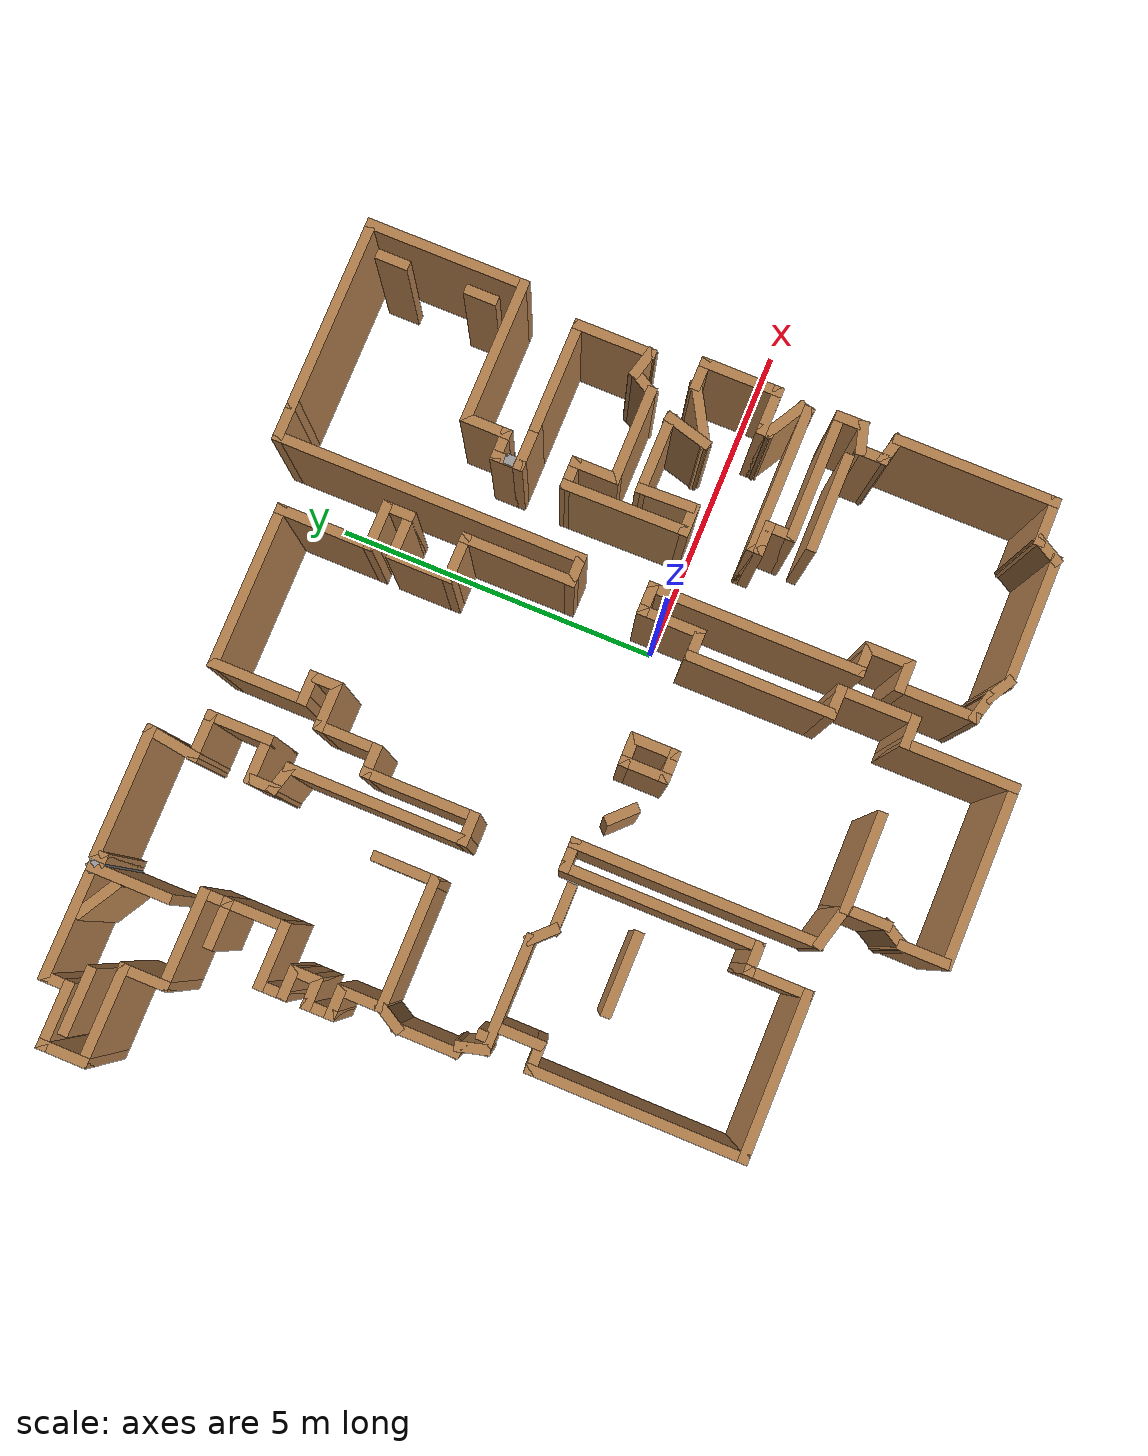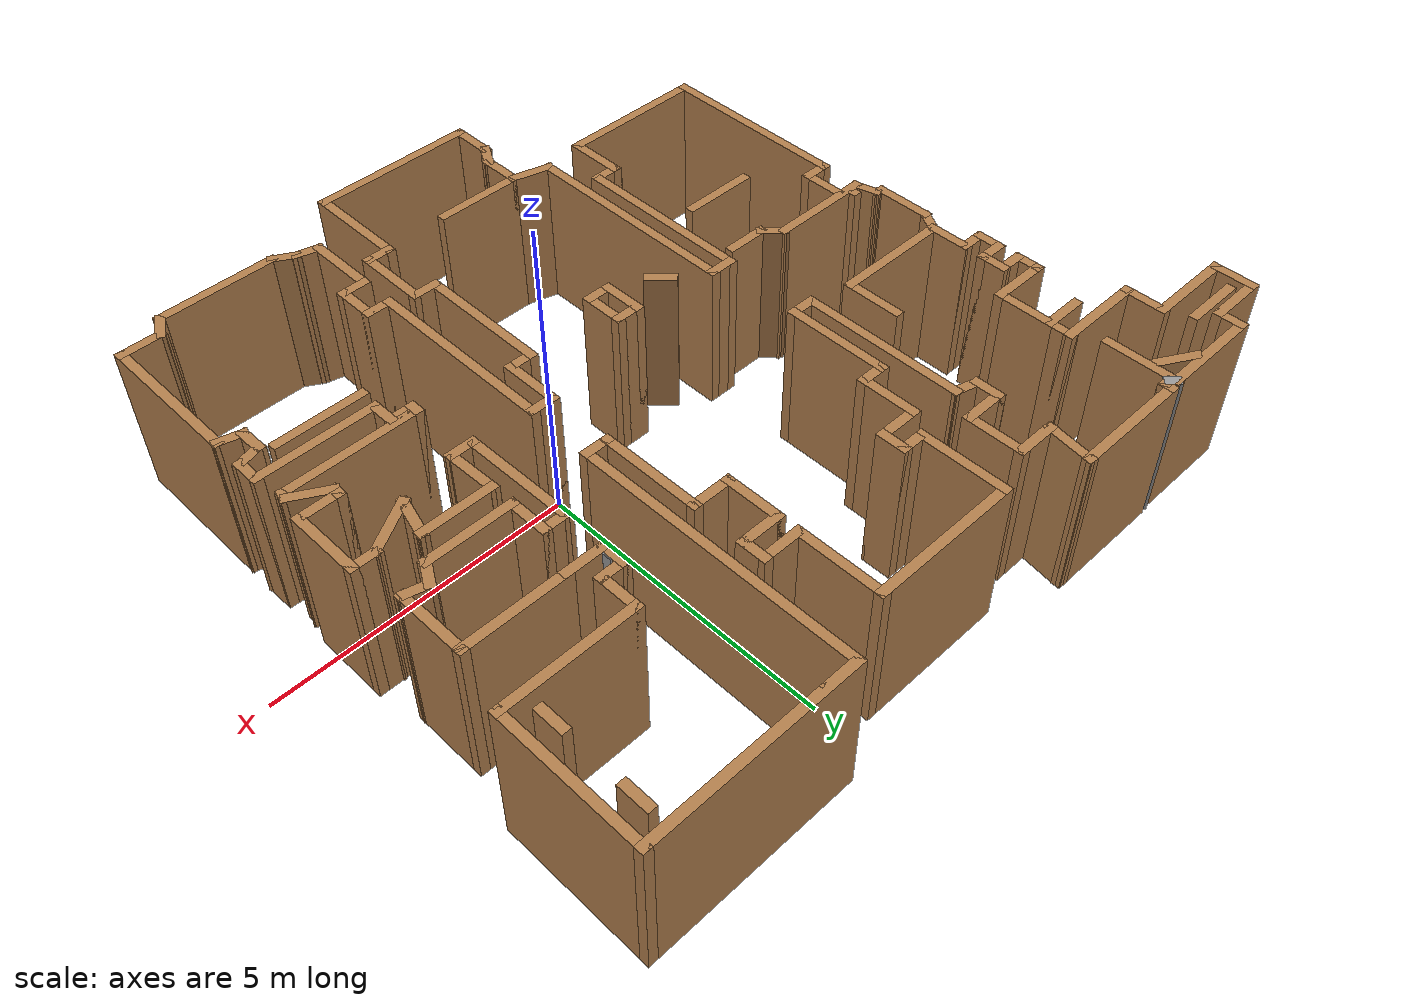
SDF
<?xml version='1.0'?>
<sdf version='1.6'>
  <model name='map_30'>
    <pose frame=''>-2.27007 0.308618 0 0 -0 0</pose>
    <link name='Wall_10'>
      <collision name='Wall_10_Collision'>
        <geometry>
          <box>
            <size>0.75 0.15 2.5</size>
          </box>
        </geometry>
        <pose frame=''>0 0 1.25 0 -0 0</pose>
      </collision>
      <visual name='Wall_10_Visual'>
        <pose frame=''>0 0 1.25 0 -0 0</pose>
        <geometry>
          <box>
            <size>0.75 0.15 2.5</size>
          </box>
        </geometry>
        <material>
          <script>
            <uri>file://media/materials/scripts/gazebo.material</uri>
            <name>Gazebo/Wood</name>
          </script>
          <ambient>1 1 1 1</ambient>
        </material>
        <meta>
          <layer>0</layer>
        </meta>
      </visual>
      <pose frame=''>-6.15506 4.97315 0 0 -0 -1.5708</pose>
    </link>
    <link name='Wall_100'>
      <collision name='Wall_100_Collision'>
        <geometry>
          <box>
            <size>0.25 0.15 2.5</size>
          </box>
        </geometry>
        <pose frame=''>0 0 1.25 0 -0 0</pose>
      </collision>
      <visual name='Wall_100_Visual'>
        <pose frame=''>0 0 1.25 0 -0 0</pose>
        <geometry>
          <box>
            <size>0.25 0.15 2.5</size>
          </box>
        </geometry>
        <material>
          <script>
            <uri>file://media/materials/scripts/gazebo.material</uri>
            <name>Gazebo/Wood</name>
          </script>
          <ambient>1 1 1 1</ambient>
        </material>
        <meta>
          <layer>0</layer>
        </meta>
      </visual>
      <pose frame=''>3.86655 -1.14749 0 0 -0 1.5708</pose>
    </link>
    <link name='Wall_101'>
      <collision name='Wall_101_Collision'>
        <geometry>
          <box>
            <size>2.25 0.15 2.5</size>
          </box>
        </geometry>
        <pose frame=''>0 0 1.25 0 -0 0</pose>
      </collision>
      <visual name='Wall_101_Visual'>
        <pose frame=''>0 0 1.25 0 -0 0</pose>
        <geometry>
          <box>
            <size>2.25 0.15 2.5</size>
          </box>
        </geometry>
        <material>
          <script>
            <uri>file://media/materials/scripts/gazebo.material</uri>
            <name>Gazebo/Wood</name>
          </script>
          <ambient>1 1 1 1</ambient>
        </material>
        <meta>
          <layer>0</layer>
        </meta>
      </visual>
      <pose frame=''>4.91655 -1.09749 0 0 -0 0</pose>
    </link>
    <link name='Wall_102'>
      <collision name='Wall_102_Collision'>
        <geometry>
          <box>
            <size>0.25 0.15 2.5</size>
          </box>
        </geometry>
        <pose frame=''>0 0 1.25 0 -0 0</pose>
      </collision>
      <visual name='Wall_102_Visual'>
        <pose frame=''>0 0 1.25 0 -0 0</pose>
        <geometry>
          <box>
            <size>0.25 0.15 2.5</size>
          </box>
        </geometry>
        <material>
          <script>
            <uri>file://media/materials/scripts/gazebo.material</uri>
            <name>Gazebo/Wood</name>
          </script>
          <ambient>1 1 1 1</ambient>
        </material>
        <meta>
          <layer>0</layer>
        </meta>
      </visual>
      <pose frame=''>5.97949 -1.04919 0 0 -0 1.309</pose>
    </link>
    <link name='Wall_103'>
      <collision name='Wall_103_Collision'>
        <geometry>
          <box>
            <size>0.75 0.15 2.5</size>
          </box>
        </geometry>
        <pose frame=''>0 0 1.25 0 -0 0</pose>
      </collision>
      <visual name='Wall_103_Visual'>
        <pose frame=''>0 0 1.25 0 -0 0</pose>
        <geometry>
          <box>
            <size>0.75 0.15 2.5</size>
          </box>
        </geometry>
        <material>
          <script>
            <uri>file://media/materials/scripts/gazebo.material</uri>
            <name>Gazebo/Wood</name>
          </script>
          <ambient>1 1 1 1</ambient>
        </material>
        <meta>
          <layer>0</layer>
        </meta>
      </visual>
      <pose frame=''>5.73262 -0.850895 0 0 -0 2.61799</pose>
    </link>
    <link name='Wall_104'>
      <collision name='Wall_104_Collision'>
        <geometry>
          <box>
            <size>0.25 0.15 2.5</size>
          </box>
        </geometry>
        <pose frame=''>0 0 1.25 0 -0 0</pose>
      </collision>
      <visual name='Wall_104_Visual'>
        <pose frame=''>0 0 1.25 0 -0 0</pose>
        <geometry>
          <box>
            <size>0.25 0.15 2.5</size>
          </box>
        </geometry>
        <material>
          <script>
            <uri>file://media/materials/scripts/gazebo.material</uri>
            <name>Gazebo/Wood</name>
          </script>
          <ambient>1 1 1 1</ambient>
        </material>
        <meta>
          <layer>0</layer>
        </meta>
      </visual>
      <pose frame=''>5.47282 -0.650895 0 0 -0 1.5708</pose>
    </link>
    <link name='Wall_105'>
      <collision name='Wall_105_Collision'>
        <geometry>
          <box>
            <size>0.75 0.15 2.5</size>
          </box>
        </geometry>
        <pose frame=''>0 0 1.25 0 -0 0</pose>
      </collision>
      <visual name='Wall_105_Visual'>
        <pose frame=''>0 0 1.25 0 -0 0</pose>
        <geometry>
          <box>
            <size>0.75 0.15 2.5</size>
          </box>
        </geometry>
        <material>
          <script>
            <uri>file://media/materials/scripts/gazebo.material</uri>
            <name>Gazebo/Wood</name>
          </script>
          <ambient>1 1 1 1</ambient>
        </material>
        <meta>
          <layer>0</layer>
        </meta>
      </visual>
      <pose frame=''>5.77282 -0.600895 0 0 -0 0</pose>
    </link>
    <link name='Wall_106'>
      <collision name='Wall_106_Collision'>
        <geometry>
          <box>
            <size>1.25 0.15 2.5</size>
          </box>
        </geometry>
        <pose frame=''>0 0 1.25 0 -0 0</pose>
      </collision>
      <visual name='Wall_106_Visual'>
        <pose frame=''>0 0 1.25 0 -0 0</pose>
        <geometry>
          <box>
            <size>1.25 0.15 2.5</size>
          </box>
        </geometry>
        <material>
          <script>
            <uri>file://media/materials/scripts/gazebo.material</uri>
            <name>Gazebo/Wood</name>
          </script>
          <ambient>1 1 1 1</ambient>
        </material>
        <meta>
          <layer>0</layer>
        </meta>
      </visual>
      <pose frame=''>6.07282 -0.050895 0 0 -0 1.5708</pose>
    </link>
    <link name='Wall_107'>
      <collision name='Wall_107_Collision'>
        <geometry>
          <box>
            <size>0.5 0.15 2.5</size>
          </box>
        </geometry>
        <pose frame=''>0 0 1.25 0 -0 0</pose>
      </collision>
      <visual name='Wall_107_Visual'>
        <pose frame=''>0 0 1.25 0 -0 0</pose>
        <geometry>
          <box>
            <size>0.5 0.15 2.5</size>
          </box>
        </geometry>
        <material>
          <script>
            <uri>file://media/materials/scripts/gazebo.material</uri>
            <name>Gazebo/Wood</name>
          </script>
          <ambient>1 1 1 1</ambient>
        </material>
        <meta>
          <layer>0</layer>
        </meta>
      </visual>
      <pose frame=''>5.89782 0.499105 0 0 -0 3.14159</pose>
    </link>
    <link name='Wall_108'>
      <collision name='Wall_108_Collision'>
        <geometry>
          <box>
            <size>1 0.15 2.5</size>
          </box>
        </geometry>
        <pose frame=''>0 0 1.25 0 -0 0</pose>
      </collision>
      <visual name='Wall_108_Visual'>
        <pose frame=''>0 0 1.25 0 -0 0</pose>
        <geometry>
          <box>
            <size>1 0.15 2.5</size>
          </box>
        </geometry>
        <material>
          <script>
            <uri>file://media/materials/scripts/gazebo.material</uri>
            <name>Gazebo/Wood</name>
          </script>
          <ambient>1 1 1 1</ambient>
        </material>
        <meta>
          <layer>0</layer>
        </meta>
      </visual>
      <pose frame=''>5.35475 0.286605 0 0 -0 -2.61799</pose>
    </link>
    <link name='Wall_109'>
      <collision name='Wall_109_Collision'>
        <geometry>
          <box>
            <size>0.75 0.15 2.5</size>
          </box>
        </geometry>
        <pose frame=''>0 0 1.25 0 -0 0</pose>
      </collision>
      <visual name='Wall_109_Visual'>
        <pose frame=''>0 0 1.25 0 -0 0</pose>
        <geometry>
          <box>
            <size>0.75 0.15 2.5</size>
          </box>
        </geometry>
        <material>
          <script>
            <uri>file://media/materials/scripts/gazebo.material</uri>
            <name>Gazebo/Wood</name>
          </script>
          <ambient>1 1 1 1</ambient>
        </material>
        <meta>
          <layer>0</layer>
        </meta>
      </visual>
      <pose frame=''>5.06434 0.363883 0 0 -0 1.309</pose>
    </link>
    <link name='Wall_112'>
      <collision name='Wall_112_Collision'>
        <geometry>
          <box>
            <size>1.25 0.15 2.5</size>
          </box>
        </geometry>
        <pose frame=''>0 0 1.25 0 -0 0</pose>
      </collision>
      <visual name='Wall_112_Visual'>
        <pose frame=''>0 0 1.25 0 -0 0</pose>
        <geometry>
          <box>
            <size>1.25 0.15 2.5</size>
          </box>
        </geometry>
        <material>
          <script>
            <uri>file://media/materials/scripts/gazebo.material</uri>
            <name>Gazebo/Wood</name>
          </script>
          <ambient>1 1 1 1</ambient>
        </material>
        <meta>
          <layer>0</layer>
        </meta>
      </visual>
      <pose frame=''>4.59199 0.653661 0 0 -0 3.14159</pose>
    </link>
    <link name='Wall_113'>
      <collision name='Wall_113_Collision'>
        <geometry>
          <box>
            <size>0.884711 0.15 2.5</size>
          </box>
        </geometry>
        <pose frame=''>0 0 1.25 0 -0 0</pose>
      </collision>
      <visual name='Wall_113_Visual'>
        <pose frame=''>0 0 1.25 0 -0 0</pose>
        <geometry>
          <box>
            <size>0.884711 0.15 2.5</size>
          </box>
        </geometry>
        <material>
          <script>
            <uri>file://media/materials/scripts/gazebo.material</uri>
            <name>Gazebo/Wood</name>
          </script>
          <ambient>1 1 1 1</ambient>
        </material>
        <meta>
          <layer>0</layer>
        </meta>
      </visual>
      <pose frame=''>4.05355 0.286487 0 0 -0 -1.53931</pose>
    </link>
    <link name='Wall_116'>
      <collision name='Wall_116_Collision'>
        <geometry>
          <box>
            <size>0.5 0.15 2.5</size>
          </box>
        </geometry>
        <pose frame=''>0 0 1.25 0 -0 0</pose>
      </collision>
      <visual name='Wall_116_Visual'>
        <pose frame=''>0 0 1.25 0 -0 0</pose>
        <geometry>
          <box>
            <size>0.5 0.15 2.5</size>
          </box>
        </geometry>
        <material>
          <script>
            <uri>file://media/materials/scripts/gazebo.material</uri>
            <name>Gazebo/Wood</name>
          </script>
          <ambient>1 1 1 1</ambient>
        </material>
        <meta>
          <layer>0</layer>
        </meta>
      </visual>
      <pose frame=''>3.89012 -0.126947 0 0 -0 3.14159</pose>
    </link>
    <link name='Wall_117'>
      <collision name='Wall_117_Collision'>
        <geometry>
          <box>
            <size>1.8845 0.15 2.5</size>
          </box>
        </geometry>
        <pose frame=''>0 0 1.25 0 -0 0</pose>
      </collision>
      <visual name='Wall_117_Visual'>
        <pose frame=''>0 0 1.25 0 -0 0</pose>
        <geometry>
          <box>
            <size>1.8845 0.15 2.5</size>
          </box>
        </geometry>
        <material>
          <script>
            <uri>file://media/materials/scripts/gazebo.material</uri>
            <name>Gazebo/Wood</name>
          </script>
          <ambient>1 1 1 1</ambient>
        </material>
        <meta>
          <layer>0</layer>
        </meta>
      </visual>
      <pose frame=''>3.70355 0.786487 0 0 -0 1.58413</pose>
    </link>
    <link name='Wall_118'>
      <collision name='Wall_118_Collision'>
        <geometry>
          <box>
            <size>0.5 0.15 2.5</size>
          </box>
        </geometry>
        <pose frame=''>0 0 1.25 0 -0 0</pose>
      </collision>
      <visual name='Wall_118_Visual'>
        <pose frame=''>0 0 1.25 0 -0 0</pose>
        <geometry>
          <box>
            <size>0.5 0.15 2.5</size>
          </box>
        </geometry>
        <material>
          <script>
            <uri>file://media/materials/scripts/gazebo.material</uri>
            <name>Gazebo/Wood</name>
          </script>
          <ambient>1 1 1 1</ambient>
        </material>
        <meta>
          <layer>0</layer>
        </meta>
      </visual>
      <pose frame=''>3.86699 1.65366 0 0 -0 0</pose>
    </link>
    <link name='Wall_121'>
      <collision name='Wall_121_Collision'>
        <geometry>
          <box>
            <size>0.75 0.15 2.5</size>
          </box>
        </geometry>
        <pose frame=''>0 0 1.25 0 -0 0</pose>
      </collision>
      <visual name='Wall_121_Visual'>
        <pose frame=''>0 0 1.25 0 -0 0</pose>
        <geometry>
          <box>
            <size>0.75 0.15 2.5</size>
          </box>
        </geometry>
        <material>
          <script>
            <uri>file://media/materials/scripts/gazebo.material</uri>
            <name>Gazebo/Wood</name>
          </script>
          <ambient>1 1 1 1</ambient>
        </material>
        <meta>
          <layer>0</layer>
        </meta>
      </visual>
      <pose frame=''>4.04199 1.35366 0 0 -0 -1.5708</pose>
    </link>
    <link name='Wall_122'>
      <collision name='Wall_122_Collision'>
        <geometry>
          <box>
            <size>1.5 0.15 2.5</size>
          </box>
        </geometry>
        <pose frame=''>0 0 1.25 0 -0 0</pose>
      </collision>
      <visual name='Wall_122_Visual'>
        <pose frame=''>0 0 1.25 0 -0 0</pose>
        <geometry>
          <box>
            <size>1.5 0.15 2.5</size>
          </box>
        </geometry>
        <material>
          <script>
            <uri>file://media/materials/scripts/gazebo.material</uri>
            <name>Gazebo/Wood</name>
          </script>
          <ambient>1 1 1 1</ambient>
        </material>
        <meta>
          <layer>0</layer>
        </meta>
      </visual>
      <pose frame=''>4.71699 1.05366 0 0 -0 0</pose>
    </link>
    <link name='Wall_123'>
      <collision name='Wall_123_Collision'>
        <geometry>
          <box>
            <size>0.5 0.15 2.5</size>
          </box>
        </geometry>
        <pose frame=''>0 0 1.25 0 -0 0</pose>
      </collision>
      <visual name='Wall_123_Visual'>
        <pose frame=''>0 0 1.25 0 -0 0</pose>
        <geometry>
          <box>
            <size>0.5 0.15 2.5</size>
          </box>
        </geometry>
        <material>
          <script>
            <uri>file://media/materials/scripts/gazebo.material</uri>
            <name>Gazebo/Wood</name>
          </script>
          <ambient>1 1 1 1</ambient>
        </material>
        <meta>
          <layer>0</layer>
        </meta>
      </visual>
      <pose frame=''>5.47949 1.20521 0 0 -0 1.0472</pose>
    </link>
    <link name='Wall_124'>
      <collision name='Wall_124_Collision'>
        <geometry>
          <box>
            <size>0.5 0.15 2.5</size>
          </box>
        </geometry>
        <pose frame=''>0 0 1.25 0 -0 0</pose>
      </collision>
      <visual name='Wall_124_Visual'>
        <pose frame=''>0 0 1.25 0 -0 0</pose>
        <geometry>
          <box>
            <size>0.5 0.15 2.5</size>
          </box>
        </geometry>
        <material>
          <script>
            <uri>file://media/materials/scripts/gazebo.material</uri>
            <name>Gazebo/Wood</name>
          </script>
          <ambient>1 1 1 1</ambient>
        </material>
        <meta>
          <layer>0</layer>
        </meta>
      </visual>
      <pose frame=''>5.73602 1.31148 0 0 -0 -0.261799</pose>
    </link>
    <link name='Wall_125'>
      <collision name='Wall_125_Collision'>
        <geometry>
          <box>
            <size>1.25 0.15 2.5</size>
          </box>
        </geometry>
        <pose frame=''>0 0 1.25 0 -0 0</pose>
      </collision>
      <visual name='Wall_125_Visual'>
        <pose frame=''>0 0 1.25 0 -0 0</pose>
        <geometry>
          <box>
            <size>1.25 0.15 2.5</size>
          </box>
        </geometry>
        <material>
          <script>
            <uri>file://media/materials/scripts/gazebo.material</uri>
            <name>Gazebo/Wood</name>
          </script>
          <ambient>1 1 1 1</ambient>
        </material>
        <meta>
          <layer>0</layer>
        </meta>
      </visual>
      <pose frame=''>5.90506 1.81618 0 0 -0 1.5708</pose>
    </link>
    <link name='Wall_126'>
      <collision name='Wall_126_Collision'>
        <geometry>
          <box>
            <size>1.75 0.15 2.5</size>
          </box>
        </geometry>
        <pose frame=''>0 0 1.25 0 -0 0</pose>
      </collision>
      <visual name='Wall_126_Visual'>
        <pose frame=''>0 0 1.25 0 -0 0</pose>
        <geometry>
          <box>
            <size>1.75 0.15 2.5</size>
          </box>
        </geometry>
        <material>
          <script>
            <uri>file://media/materials/scripts/gazebo.material</uri>
            <name>Gazebo/Wood</name>
          </script>
          <ambient>1 1 1 1</ambient>
        </material>
        <meta>
          <layer>0</layer>
        </meta>
      </visual>
      <pose frame=''>5.10506 2.36618 0 0 -0 3.14159</pose>
    </link>
    <link name='Wall_128'>
      <collision name='Wall_128_Collision'>
        <geometry>
          <box>
            <size>0.15 0.15 2.5</size>
          </box>
        </geometry>
        <pose frame=''>0 0 1.25 0 -0 0</pose>
      </collision>
      <visual name='Wall_128_Visual'>
        <pose frame=''>0 0 1.25 0 -0 0</pose>
        <geometry>
          <box>
            <size>0.15 0.15 2.5</size>
          </box>
        </geometry>
        <material>
          <script>
            <uri>file://media/materials/scripts/gazebo.material</uri>
            <name>Gazebo/Grey</name>
          </script>
          <ambient>1 1 1 1</ambient>
        </material>
        <meta>
          <layer>0</layer>
        </meta>
      </visual>
      <pose frame=''>3.7255 2.52147 0 0 -0 0</pose>
    </link>
    <link name='Wall_13'>
      <collision name='Wall_13_Collision'>
        <geometry>
          <box>
            <size>1.5 0.15 2.5</size>
          </box>
        </geometry>
        <pose frame=''>0 0 1.25 0 -0 0</pose>
      </collision>
      <visual name='Wall_13_Visual'>
        <pose frame=''>0 0 1.25 0 -0 0</pose>
        <geometry>
          <box>
            <size>1.5 0.15 2.5</size>
          </box>
        </geometry>
        <material>
          <script>
            <uri>file://media/materials/scripts/gazebo.material</uri>
            <name>Gazebo/Wood</name>
          </script>
          <ambient>1 1 1 1</ambient>
        </material>
        <meta>
          <layer>0</layer>
        </meta>
      </visual>
      <pose frame=''>-5.48006 4.67315 0 0 -0 0</pose>
    </link>
    <link name='Wall_130'>
      <collision name='Wall_130_Collision'>
        <geometry>
          <box>
            <size>0.75 0.15 2.5</size>
          </box>
        </geometry>
        <pose frame=''>0 0 1.25 0 -0 0</pose>
      </collision>
      <visual name='Wall_130_Visual'>
        <pose frame=''>0 0 1.25 0 -0 0</pose>
        <geometry>
          <box>
            <size>0.75 0.15 2.5</size>
          </box>
        </geometry>
        <material>
          <script>
            <uri>file://media/materials/scripts/gazebo.material</uri>
            <name>Gazebo/Wood</name>
          </script>
          <ambient>1 1 1 1</ambient>
        </material>
        <meta>
          <layer>0</layer>
        </meta>
      </visual>
      <pose frame=''>4.00506 2.36618 0 0 -0 3.14159</pose>
    </link>
    <link name='Wall_131'>
      <collision name='Wall_131_Collision'>
        <geometry>
          <box>
            <size>0.5 0.15 2.5</size>
          </box>
        </geometry>
        <pose frame=''>0 0 1.25 0 -0 0</pose>
      </collision>
      <visual name='Wall_131_Visual'>
        <pose frame=''>0 0 1.25 0 -0 0</pose>
        <geometry>
          <box>
            <size>0.5 0.15 2.5</size>
          </box>
        </geometry>
        <material>
          <script>
            <uri>file://media/materials/scripts/gazebo.material</uri>
            <name>Gazebo/Wood</name>
          </script>
          <ambient>1 1 1 1</ambient>
        </material>
        <meta>
          <layer>0</layer>
        </meta>
      </visual>
      <pose frame=''>3.70506 2.54118 0 0 -0 1.5708</pose>
    </link>
    <link name='Wall_132'>
      <collision name='Wall_132_Collision'>
        <geometry>
          <box>
            <size>0.5 0.15 2.5</size>
          </box>
        </geometry>
        <pose frame=''>0 0 1.25 0 -0 0</pose>
      </collision>
      <visual name='Wall_132_Visual'>
        <pose frame=''>0 0 1.25 0 -0 0</pose>
        <geometry>
          <box>
            <size>0.5 0.15 2.5</size>
          </box>
        </geometry>
        <material>
          <script>
            <uri>file://media/materials/scripts/gazebo.material</uri>
            <name>Gazebo/Wood</name>
          </script>
          <ambient>1 1 1 1</ambient>
        </material>
        <meta>
          <layer>0</layer>
        </meta>
      </visual>
      <pose frame=''>3.88006 2.71618 0 0 -0 0</pose>
    </link>
    <link name='Wall_133'>
      <collision name='Wall_133_Collision'>
        <geometry>
          <box>
            <size>0.75 0.15 2.5</size>
          </box>
        </geometry>
        <pose frame=''>0 0 1.25 0 -0 0</pose>
      </collision>
      <visual name='Wall_133_Visual'>
        <pose frame=''>0 0 1.25 0 -0 0</pose>
        <geometry>
          <box>
            <size>0.75 0.15 2.5</size>
          </box>
        </geometry>
        <material>
          <script>
            <uri>file://media/materials/scripts/gazebo.material</uri>
            <name>Gazebo/Wood</name>
          </script>
          <ambient>1 1 1 1</ambient>
        </material>
        <meta>
          <layer>0</layer>
        </meta>
      </visual>
      <pose frame=''>4.05506 3.01618 0 0 -0 1.5708</pose>
    </link>
    <link name='Wall_134'>
      <collision name='Wall_134_Collision'>
        <geometry>
          <box>
            <size>2.25 0.15 2.5</size>
          </box>
        </geometry>
        <pose frame=''>0 0 1.25 0 -0 0</pose>
      </collision>
      <visual name='Wall_134_Visual'>
        <pose frame=''>0 0 1.25 0 -0 0</pose>
        <geometry>
          <box>
            <size>2.25 0.15 2.5</size>
          </box>
        </geometry>
        <material>
          <script>
            <uri>file://media/materials/scripts/gazebo.material</uri>
            <name>Gazebo/Wood</name>
          </script>
          <ambient>1 1 1 1</ambient>
        </material>
        <meta>
          <layer>0</layer>
        </meta>
      </visual>
      <pose frame=''>5.10506 3.31618 0 0 -0 0</pose>
    </link>
    <link name='Wall_135'>
      <collision name='Wall_135_Collision'>
        <geometry>
          <box>
            <size>2.5 0.15 2.5</size>
          </box>
        </geometry>
        <pose frame=''>0 0 1.25 0 -0 0</pose>
      </collision>
      <visual name='Wall_135_Visual'>
        <pose frame=''>0 0 1.25 0 -0 0</pose>
        <geometry>
          <box>
            <size>2.5 0.15 2.5</size>
          </box>
        </geometry>
        <material>
          <script>
            <uri>file://media/materials/scripts/gazebo.material</uri>
            <name>Gazebo/Wood</name>
          </script>
          <ambient>1 1 1 1</ambient>
        </material>
        <meta>
          <layer>0</layer>
        </meta>
      </visual>
      <pose frame=''>6.15506 4.49118 0 0 -0 1.5708</pose>
    </link>
    <link name='Wall_137'>
      <collision name='Wall_137_Collision'>
        <geometry>
          <box>
            <size>0.15 0.15 2.5</size>
          </box>
        </geometry>
        <pose frame=''>0 0 1.25 0 -0 0</pose>
      </collision>
      <visual name='Wall_137_Visual'>
        <pose frame=''>0 0 1.25 0 -0 0</pose>
        <geometry>
          <box>
            <size>0.15 0.15 2.5</size>
          </box>
        </geometry>
        <material>
          <script>
            <uri>file://media/materials/scripts/gazebo.material</uri>
            <name>Gazebo/Wood</name>
          </script>
          <ambient>1 1 1 1</ambient>
        </material>
        <meta>
          <layer>0</layer>
        </meta>
      </visual>
      <pose frame=''>3.30506 5.66618 0 0 -0 0</pose>
    </link>
    <link name='Wall_14'>
      <collision name='Wall_14_Collision'>
        <geometry>
          <box>
            <size>0.75 0.15 2.5</size>
          </box>
        </geometry>
        <pose frame=''>0 0 1.25 0 -0 0</pose>
      </collision>
      <visual name='Wall_14_Visual'>
        <pose frame=''>0 0 1.25 0 -0 0</pose>
        <geometry>
          <box>
            <size>0.75 0.15 2.5</size>
          </box>
        </geometry>
        <material>
          <script>
            <uri>file://media/materials/scripts/gazebo.material</uri>
            <name>Gazebo/Wood</name>
          </script>
          <ambient>1 1 1 1</ambient>
        </material>
        <meta>
          <layer>0</layer>
        </meta>
      </visual>
      <pose frame=''>-4.80506 4.37315 0 0 -0 -1.5708</pose>
    </link>
    <link name='Wall_143'>
      <collision name='Wall_143_Collision'>
        <geometry>
          <box>
            <size>3.5 0.15 2.5</size>
          </box>
        </geometry>
        <pose frame=''>0 0 1.25 0 -0 0</pose>
      </collision>
      <visual name='Wall_143_Visual'>
        <pose frame=''>0 0 1.25 0 -0 0</pose>
        <geometry>
          <box>
            <size>3.5 0.15 2.5</size>
          </box>
        </geometry>
        <material>
          <script>
            <uri>file://media/materials/scripts/gazebo.material</uri>
            <name>Gazebo/Wood</name>
          </script>
          <ambient>1 1 1 1</ambient>
        </material>
        <meta>
          <layer>0</layer>
        </meta>
      </visual>
      <pose frame=''>4.48006 5.66618 0 0 -0 3.14159</pose>
    </link>
    <link name='Wall_144'>
      <collision name='Wall_144_Collision'>
        <geometry>
          <box>
            <size>4.75 0.15 2.5</size>
          </box>
        </geometry>
        <pose frame=''>0 0 1.25 0 -0 0</pose>
      </collision>
      <visual name='Wall_144_Visual'>
        <pose frame=''>0 0 1.25 0 -0 0</pose>
        <geometry>
          <box>
            <size>4.75 0.15 2.5</size>
          </box>
        </geometry>
        <material>
          <script>
            <uri>file://media/materials/scripts/gazebo.material</uri>
            <name>Gazebo/Wood</name>
          </script>
          <ambient>1 1 1 1</ambient>
        </material>
        <meta>
          <layer>0</layer>
        </meta>
      </visual>
      <pose frame=''>2.80506 3.36618 0 0 -0 -1.5708</pose>
    </link>
    <link name='Wall_145'>
      <collision name='Wall_145_Collision'>
        <geometry>
          <box>
            <size>0.5 0.15 2.5</size>
          </box>
        </geometry>
        <pose frame=''>0 0 1.25 0 -0 0</pose>
      </collision>
      <visual name='Wall_145_Visual'>
        <pose frame=''>0 0 1.25 0 -0 0</pose>
        <geometry>
          <box>
            <size>0.5 0.15 2.5</size>
          </box>
        </geometry>
        <material>
          <script>
            <uri>file://media/materials/scripts/gazebo.material</uri>
            <name>Gazebo/Wood</name>
          </script>
          <ambient>1 1 1 1</ambient>
        </material>
        <meta>
          <layer>0</layer>
        </meta>
      </visual>
      <pose frame=''>2.63006 1.06618 0 0 -0 3.14159</pose>
    </link>
    <link name='Wall_146'>
      <collision name='Wall_146_Collision'>
        <geometry>
          <box>
            <size>1.75 0.15 2.5</size>
          </box>
        </geometry>
        <pose frame=''>0 0 1.25 0 -0 0</pose>
      </collision>
      <visual name='Wall_146_Visual'>
        <pose frame=''>0 0 1.25 0 -0 0</pose>
        <geometry>
          <box>
            <size>1.75 0.15 2.5</size>
          </box>
        </geometry>
        <material>
          <script>
            <uri>file://media/materials/scripts/gazebo.material</uri>
            <name>Gazebo/Wood</name>
          </script>
          <ambient>1 1 1 1</ambient>
        </material>
        <meta>
          <layer>0</layer>
        </meta>
      </visual>
      <pose frame=''>2.45506 1.86618 0 0 -0 1.5708</pose>
    </link>
    <link name='Wall_147'>
      <collision name='Wall_147_Collision'>
        <geometry>
          <box>
            <size>0.75 0.15 2.5</size>
          </box>
        </geometry>
        <pose frame=''>0 0 1.25 0 -0 0</pose>
      </collision>
      <visual name='Wall_147_Visual'>
        <pose frame=''>0 0 1.25 0 -0 0</pose>
        <geometry>
          <box>
            <size>0.75 0.15 2.5</size>
          </box>
        </geometry>
        <material>
          <script>
            <uri>file://media/materials/scripts/gazebo.material</uri>
            <name>Gazebo/Wood</name>
          </script>
          <ambient>1 1 1 1</ambient>
        </material>
        <meta>
          <layer>0</layer>
        </meta>
      </visual>
      <pose frame=''>2.15506 2.66618 0 0 -0 3.14159</pose>
    </link>
    <link name='Wall_148'>
      <collision name='Wall_148_Collision'>
        <geometry>
          <box>
            <size>1 0.15 2.5</size>
          </box>
        </geometry>
        <pose frame=''>0 0 1.25 0 -0 0</pose>
      </collision>
      <visual name='Wall_148_Visual'>
        <pose frame=''>0 0 1.25 0 -0 0</pose>
        <geometry>
          <box>
            <size>1 0.15 2.5</size>
          </box>
        </geometry>
        <material>
          <script>
            <uri>file://media/materials/scripts/gazebo.material</uri>
            <name>Gazebo/Wood</name>
          </script>
          <ambient>1 1 1 1</ambient>
        </material>
        <meta>
          <layer>0</layer>
        </meta>
      </visual>
      <pose frame=''>1.85506 3.09118 0 0 -0 1.5708</pose>
    </link>
    <link name='Wall_149'>
      <collision name='Wall_149_Collision'>
        <geometry>
          <box>
            <size>0.75 0.15 2.5</size>
          </box>
        </geometry>
        <pose frame=''>0 0 1.25 0 -0 0</pose>
      </collision>
      <visual name='Wall_149_Visual'>
        <pose frame=''>0 0 1.25 0 -0 0</pose>
        <geometry>
          <box>
            <size>0.75 0.15 2.5</size>
          </box>
        </geometry>
        <material>
          <script>
            <uri>file://media/materials/scripts/gazebo.material</uri>
            <name>Gazebo/Wood</name>
          </script>
          <ambient>1 1 1 1</ambient>
        </material>
        <meta>
          <layer>0</layer>
        </meta>
      </visual>
      <pose frame=''>2.15506 3.51618 0 0 -0 0</pose>
    </link>
    <link name='Wall_15'>
      <collision name='Wall_15_Collision'>
        <geometry>
          <box>
            <size>1.5 0.15 2.5</size>
          </box>
        </geometry>
        <pose frame=''>0 0 1.25 0 -0 0</pose>
      </collision>
      <visual name='Wall_15_Visual'>
        <pose frame=''>0 0 1.25 0 -0 0</pose>
        <geometry>
          <box>
            <size>1.5 0.15 2.5</size>
          </box>
        </geometry>
        <material>
          <script>
            <uri>file://media/materials/scripts/gazebo.material</uri>
            <name>Gazebo/Wood</name>
          </script>
          <ambient>1 1 1 1</ambient>
        </material>
        <meta>
          <layer>0</layer>
        </meta>
      </visual>
      <pose frame=''>-4.13006 4.07315 0 0 -0 0</pose>
    </link>
    <link name='Wall_150'>
      <collision name='Wall_150_Collision'>
        <geometry>
          <box>
            <size>0.5 0.15 2.5</size>
          </box>
        </geometry>
        <pose frame=''>0 0 1.25 0 -0 0</pose>
      </collision>
      <visual name='Wall_150_Visual'>
        <pose frame=''>0 0 1.25 0 -0 0</pose>
        <geometry>
          <box>
            <size>0.5 0.15 2.5</size>
          </box>
        </geometry>
        <material>
          <script>
            <uri>file://media/materials/scripts/gazebo.material</uri>
            <name>Gazebo/Wood</name>
          </script>
          <ambient>1 1 1 1</ambient>
        </material>
        <meta>
          <layer>0</layer>
        </meta>
      </visual>
      <pose frame=''>2.45506 3.69118 0 0 -0 1.5708</pose>
    </link>
    <link name='Wall_151'>
      <collision name='Wall_151_Collision'>
        <geometry>
          <box>
            <size>0.75 0.15 2.5</size>
          </box>
        </geometry>
        <pose frame=''>0 0 1.25 0 -0 0</pose>
      </collision>
      <visual name='Wall_151_Visual'>
        <pose frame=''>0 0 1.25 0 -0 0</pose>
        <geometry>
          <box>
            <size>0.75 0.15 2.5</size>
          </box>
        </geometry>
        <material>
          <script>
            <uri>file://media/materials/scripts/gazebo.material</uri>
            <name>Gazebo/Wood</name>
          </script>
          <ambient>1 1 1 1</ambient>
        </material>
        <meta>
          <layer>0</layer>
        </meta>
      </visual>
      <pose frame=''>2.15506 3.86618 0 0 -0 3.14159</pose>
    </link>
    <link name='Wall_152'>
      <collision name='Wall_152_Collision'>
        <geometry>
          <box>
            <size>1.5 0.15 2.5</size>
          </box>
        </geometry>
        <pose frame=''>0 0 1.25 0 -0 0</pose>
      </collision>
      <visual name='Wall_152_Visual'>
        <pose frame=''>0 0 1.25 0 -0 0</pose>
        <geometry>
          <box>
            <size>1.5 0.15 2.5</size>
          </box>
        </geometry>
        <material>
          <script>
            <uri>file://media/materials/scripts/gazebo.material</uri>
            <name>Gazebo/Wood</name>
          </script>
          <ambient>1 1 1 1</ambient>
        </material>
        <meta>
          <layer>0</layer>
        </meta>
      </visual>
      <pose frame=''>1.85506 4.54118 0 0 -0 1.5708</pose>
    </link>
    <link name='Wall_153'>
      <collision name='Wall_153_Collision'>
        <geometry>
          <box>
            <size>2.5 0.15 2.5</size>
          </box>
        </geometry>
        <pose frame=''>0 0 1.25 0 -0 0</pose>
      </collision>
      <visual name='Wall_153_Visual'>
        <pose frame=''>0 0 1.25 0 -0 0</pose>
        <geometry>
          <box>
            <size>2.5 0.15 2.5</size>
          </box>
        </geometry>
        <material>
          <script>
            <uri>file://media/materials/scripts/gazebo.material</uri>
            <name>Gazebo/Wood</name>
          </script>
          <ambient>1 1 1 1</ambient>
        </material>
        <meta>
          <layer>0</layer>
        </meta>
      </visual>
      <pose frame=''>0.680059 5.21618 0 0 -0 3.14159</pose>
    </link>
    <link name='Wall_154'>
      <collision name='Wall_154_Collision'>
        <geometry>
          <box>
            <size>1.5 0.15 2.5</size>
          </box>
        </geometry>
        <pose frame=''>0 0 1.25 0 -0 0</pose>
      </collision>
      <visual name='Wall_154_Visual'>
        <pose frame=''>0 0 1.25 0 -0 0</pose>
        <geometry>
          <box>
            <size>1.5 0.15 2.5</size>
          </box>
        </geometry>
        <material>
          <script>
            <uri>file://media/materials/scripts/gazebo.material</uri>
            <name>Gazebo/Wood</name>
          </script>
          <ambient>1 1 1 1</ambient>
        </material>
        <meta>
          <layer>0</layer>
        </meta>
      </visual>
      <pose frame=''>-0.494941 4.54118 0 0 -0 -1.5708</pose>
    </link>
    <link name='Wall_155'>
      <collision name='Wall_155_Collision'>
        <geometry>
          <box>
            <size>0.5 0.15 2.5</size>
          </box>
        </geometry>
        <pose frame=''>0 0 1.25 0 -0 0</pose>
      </collision>
      <visual name='Wall_155_Visual'>
        <pose frame=''>0 0 1.25 0 -0 0</pose>
        <geometry>
          <box>
            <size>0.5 0.15 2.5</size>
          </box>
        </geometry>
        <material>
          <script>
            <uri>file://media/materials/scripts/gazebo.material</uri>
            <name>Gazebo/Wood</name>
          </script>
          <ambient>1 1 1 1</ambient>
        </material>
        <meta>
          <layer>0</layer>
        </meta>
      </visual>
      <pose frame=''>-0.319941 3.86618 0 0 -0 0</pose>
    </link>
    <link name='Wall_156'>
      <collision name='Wall_156_Collision'>
        <geometry>
          <box>
            <size>0.5 0.15 2.5</size>
          </box>
        </geometry>
        <pose frame=''>0 0 1.25 0 -0 0</pose>
      </collision>
      <visual name='Wall_156_Visual'>
        <pose frame=''>0 0 1.25 0 -0 0</pose>
        <geometry>
          <box>
            <size>0.5 0.15 2.5</size>
          </box>
        </geometry>
        <material>
          <script>
            <uri>file://media/materials/scripts/gazebo.material</uri>
            <name>Gazebo/Wood</name>
          </script>
          <ambient>1 1 1 1</ambient>
        </material>
        <meta>
          <layer>0</layer>
        </meta>
      </visual>
      <pose frame=''>-0.14494 3.69118 0 0 -0 -1.5708</pose>
    </link>
    <link name='Wall_157'>
      <collision name='Wall_157_Collision'>
        <geometry>
          <box>
            <size>0.75 0.15 2.5</size>
          </box>
        </geometry>
        <pose frame=''>0 0 1.25 0 -0 0</pose>
      </collision>
      <visual name='Wall_157_Visual'>
        <pose frame=''>0 0 1.25 0 -0 0</pose>
        <geometry>
          <box>
            <size>0.75 0.15 2.5</size>
          </box>
        </geometry>
        <material>
          <script>
            <uri>file://media/materials/scripts/gazebo.material</uri>
            <name>Gazebo/Wood</name>
          </script>
          <ambient>1 1 1 1</ambient>
        </material>
        <meta>
          <layer>0</layer>
        </meta>
      </visual>
      <pose frame=''>-0.444941 3.51618 0 0 -0 3.14159</pose>
    </link>
    <link name='Wall_158'>
      <collision name='Wall_158_Collision'>
        <geometry>
          <box>
            <size>1 0.15 2.5</size>
          </box>
        </geometry>
        <pose frame=''>0 0 1.25 0 -0 0</pose>
      </collision>
      <visual name='Wall_158_Visual'>
        <pose frame=''>0 0 1.25 0 -0 0</pose>
        <geometry>
          <box>
            <size>1 0.15 2.5</size>
          </box>
        </geometry>
        <material>
          <script>
            <uri>file://media/materials/scripts/gazebo.material</uri>
            <name>Gazebo/Wood</name>
          </script>
          <ambient>1 1 1 1</ambient>
        </material>
        <meta>
          <layer>0</layer>
        </meta>
      </visual>
      <pose frame=''>-0.744941 3.09118 0 0 -0 -1.5708</pose>
    </link>
    <link name='Wall_16'>
      <collision name='Wall_16_Collision'>
        <geometry>
          <box>
            <size>0.5 0.15 2.5</size>
          </box>
        </geometry>
        <pose frame=''>0 0 1.25 0 -0 0</pose>
      </collision>
      <visual name='Wall_16_Visual'>
        <pose frame=''>0 0 1.25 0 -0 0</pose>
        <geometry>
          <box>
            <size>0.5 0.15 2.5</size>
          </box>
        </geometry>
        <material>
          <script>
            <uri>file://media/materials/scripts/gazebo.material</uri>
            <name>Gazebo/Wood</name>
          </script>
          <ambient>1 1 1 1</ambient>
        </material>
        <meta>
          <layer>0</layer>
        </meta>
      </visual>
      <pose frame=''>-3.45506 3.89815 0 0 -0 -1.5708</pose>
    </link>
    <link name='Wall_161'>
      <collision name='Wall_161_Collision'>
        <geometry>
          <box>
            <size>0.5 0.15 2.5</size>
          </box>
        </geometry>
        <pose frame=''>0 0 1.25 0 -0 0</pose>
      </collision>
      <visual name='Wall_161_Visual'>
        <pose frame=''>0 0 1.25 0 -0 0</pose>
        <geometry>
          <box>
            <size>0.5 0.15 2.5</size>
          </box>
        </geometry>
        <material>
          <script>
            <uri>file://media/materials/scripts/gazebo.material</uri>
            <name>Gazebo/Wood</name>
          </script>
          <ambient>1 1 1 1</ambient>
        </material>
        <meta>
          <layer>0</layer>
        </meta>
      </visual>
      <pose frame=''>-0.919941 2.66618 0 0 -0 3.14159</pose>
    </link>
    <link name='Wall_162'>
      <collision name='Wall_162_Collision'>
        <geometry>
          <box>
            <size>1.75 0.15 2.5</size>
          </box>
        </geometry>
        <pose frame=''>0 0 1.25 0 -0 0</pose>
      </collision>
      <visual name='Wall_162_Visual'>
        <pose frame=''>0 0 1.25 0 -0 0</pose>
        <geometry>
          <box>
            <size>1.75 0.15 2.5</size>
          </box>
        </geometry>
        <material>
          <script>
            <uri>file://media/materials/scripts/gazebo.material</uri>
            <name>Gazebo/Wood</name>
          </script>
          <ambient>1 1 1 1</ambient>
        </material>
        <meta>
          <layer>0</layer>
        </meta>
      </visual>
      <pose frame=''>-1.09494 1.86618 0 0 -0 -1.5708</pose>
    </link>
    <link name='Wall_163'>
      <collision name='Wall_163_Collision'>
        <geometry>
          <box>
            <size>0.5 0.15 2.5</size>
          </box>
        </geometry>
        <pose frame=''>0 0 1.25 0 -0 0</pose>
      </collision>
      <visual name='Wall_163_Visual'>
        <pose frame=''>0 0 1.25 0 -0 0</pose>
        <geometry>
          <box>
            <size>0.5 0.15 2.5</size>
          </box>
        </geometry>
        <material>
          <script>
            <uri>file://media/materials/scripts/gazebo.material</uri>
            <name>Gazebo/Wood</name>
          </script>
          <ambient>1 1 1 1</ambient>
        </material>
        <meta>
          <layer>0</layer>
        </meta>
      </visual>
      <pose frame=''>-1.26994 1.06618 0 0 -0 3.14159</pose>
    </link>
    <link name='Wall_164'>
      <collision name='Wall_164_Collision'>
        <geometry>
          <box>
            <size>2.75 0.15 2.5</size>
          </box>
        </geometry>
        <pose frame=''>0 0 1.25 0 -0 0</pose>
      </collision>
      <visual name='Wall_164_Visual'>
        <pose frame=''>0 0 1.25 0 -0 0</pose>
        <geometry>
          <box>
            <size>2.75 0.15 2.5</size>
          </box>
        </geometry>
        <material>
          <script>
            <uri>file://media/materials/scripts/gazebo.material</uri>
            <name>Gazebo/Wood</name>
          </script>
          <ambient>1 1 1 1</ambient>
        </material>
        <meta>
          <layer>0</layer>
        </meta>
      </visual>
      <pose frame=''>-1.44494 2.36618 0 0 -0 1.5708</pose>
    </link>
    <link name='Wall_165'>
      <collision name='Wall_165_Collision'>
        <geometry>
          <box>
            <size>0.5 0.15 2.5</size>
          </box>
        </geometry>
        <pose frame=''>0 0 1.25 0 -0 0</pose>
      </collision>
      <visual name='Wall_165_Visual'>
        <pose frame=''>0 0 1.25 0 -0 0</pose>
        <geometry>
          <box>
            <size>0.5 0.15 2.5</size>
          </box>
        </geometry>
        <material>
          <script>
            <uri>file://media/materials/scripts/gazebo.material</uri>
            <name>Gazebo/Wood</name>
          </script>
          <ambient>1 1 1 1</ambient>
        </material>
        <meta>
          <layer>0</layer>
        </meta>
      </visual>
      <pose frame=''>-1.61398 3.71148 0 0 -0 2.87979</pose>
    </link>
    <link name='Wall_166'>
      <collision name='Wall_166_Collision'>
        <geometry>
          <box>
            <size>0.5 0.15 2.5</size>
          </box>
        </geometry>
        <pose frame=''>0 0 1.25 0 -0 0</pose>
      </collision>
      <visual name='Wall_166_Visual'>
        <pose frame=''>0 0 1.25 0 -0 0</pose>
        <geometry>
          <box>
            <size>0.5 0.15 2.5</size>
          </box>
        </geometry>
        <material>
          <script>
            <uri>file://media/materials/scripts/gazebo.material</uri>
            <name>Gazebo/Wood</name>
          </script>
          <ambient>1 1 1 1</ambient>
        </material>
        <meta>
          <layer>0</layer>
        </meta>
      </visual>
      <pose frame=''>-1.78302 3.93177 0 0 -0 1.5708</pose>
    </link>
    <link name='Wall_17'>
      <collision name='Wall_17_Collision'>
        <geometry>
          <box>
            <size>0.75 0.15 2.5</size>
          </box>
        </geometry>
        <pose frame=''>0 0 1.25 0 -0 0</pose>
      </collision>
      <visual name='Wall_17_Visual'>
        <pose frame=''>0 0 1.25 0 -0 0</pose>
        <geometry>
          <box>
            <size>0.75 0.15 2.5</size>
          </box>
        </geometry>
        <material>
          <script>
            <uri>file://media/materials/scripts/gazebo.material</uri>
            <name>Gazebo/Wood</name>
          </script>
          <ambient>1 1 1 1</ambient>
        </material>
        <meta>
          <layer>0</layer>
        </meta>
      </visual>
      <pose frame=''>-3.75506 3.72315 0 0 -0 3.14159</pose>
    </link>
    <link name='Wall_171'>
      <collision name='Wall_171_Collision'>
        <geometry>
          <box>
            <size>0.75 0.15 2.5</size>
          </box>
        </geometry>
        <pose frame=''>0 0 1.25 0 -0 0</pose>
      </collision>
      <visual name='Wall_171_Visual'>
        <pose frame=''>0 0 1.25 0 -0 0</pose>
        <geometry>
          <box>
            <size>0.75 0.15 2.5</size>
          </box>
        </geometry>
        <material>
          <script>
            <uri>file://media/materials/scripts/gazebo.material</uri>
            <name>Gazebo/Wood</name>
          </script>
          <ambient>1 1 1 1</ambient>
        </material>
        <meta>
          <layer>0</layer>
        </meta>
      </visual>
      <pose frame=''>-1.48301 4.10677 0 0 -0 0</pose>
    </link>
    <link name='Wall_172'>
      <collision name='Wall_172_Collision'>
        <geometry>
          <box>
            <size>1 0.15 2.5</size>
          </box>
        </geometry>
        <pose frame=''>0 0 1.25 0 -0 0</pose>
      </collision>
      <visual name='Wall_172_Visual'>
        <pose frame=''>0 0 1.25 0 -0 0</pose>
        <geometry>
          <box>
            <size>1 0.15 2.5</size>
          </box>
        </geometry>
        <material>
          <script>
            <uri>file://media/materials/scripts/gazebo.material</uri>
            <name>Gazebo/Wood</name>
          </script>
          <ambient>1 1 1 1</ambient>
        </material>
        <meta>
          <layer>0</layer>
        </meta>
      </visual>
      <pose frame=''>-1.18301 4.53177 0 0 -0 1.5708</pose>
    </link>
    <link name='Wall_173'>
      <collision name='Wall_173_Collision'>
        <geometry>
          <box>
            <size>0.75 0.15 2.5</size>
          </box>
        </geometry>
        <pose frame=''>0 0 1.25 0 -0 0</pose>
      </collision>
      <visual name='Wall_173_Visual'>
        <pose frame=''>0 0 1.25 0 -0 0</pose>
        <geometry>
          <box>
            <size>0.75 0.15 2.5</size>
          </box>
        </geometry>
        <material>
          <script>
            <uri>file://media/materials/scripts/gazebo.material</uri>
            <name>Gazebo/Wood</name>
          </script>
          <ambient>1 1 1 1</ambient>
        </material>
        <meta>
          <layer>0</layer>
        </meta>
      </visual>
      <pose frame=''>-1.48301 4.95677 0 0 -0 3.14159</pose>
    </link>
    <link name='Wall_174'>
      <collision name='Wall_174_Collision'>
        <geometry>
          <box>
            <size>0.852629 0.15 2.5</size>
          </box>
        </geometry>
        <pose frame=''>0 0 1.25 0 -0 0</pose>
      </collision>
      <visual name='Wall_174_Visual'>
        <pose frame=''>0 0 1.25 0 -0 0</pose>
        <geometry>
          <box>
            <size>0.852629 0.15 2.5</size>
          </box>
        </geometry>
        <material>
          <script>
            <uri>file://media/materials/scripts/gazebo.material</uri>
            <name>Gazebo/Wood</name>
          </script>
          <ambient>1 1 1 1</ambient>
        </material>
        <meta>
          <layer>0</layer>
        </meta>
      </visual>
      <pose frame=''>-1.73368 5.3046 0 0 -0 1.42991</pose>
    </link>
    <link name='Wall_176'>
      <collision name='Wall_176_Collision'>
        <geometry>
          <box>
            <size>1.25 0.15 2.5</size>
          </box>
        </geometry>
        <pose frame=''>0 0 1.25 0 -0 0</pose>
      </collision>
      <visual name='Wall_176_Visual'>
        <pose frame=''>0 0 1.25 0 -0 0</pose>
        <geometry>
          <box>
            <size>1.25 0.15 2.5</size>
          </box>
        </geometry>
        <material>
          <script>
            <uri>file://media/materials/scripts/gazebo.material</uri>
            <name>Gazebo/Wood</name>
          </script>
          <ambient>1 1 1 1</ambient>
        </material>
        <meta>
          <layer>0</layer>
        </meta>
      </visual>
      <pose frame=''>-3.70506 5.07315 0 0 -0 -1.5708</pose>
    </link>
    <link name='Wall_180'>
      <collision name='Wall_180_Collision'>
        <geometry>
          <box>
            <size>1 0.15 2.5</size>
          </box>
        </geometry>
        <pose frame=''>0 0 1.25 0 -0 0</pose>
      </collision>
      <visual name='Wall_180_Visual'>
        <pose frame=''>0 0 1.25 0 -0 0</pose>
        <geometry>
          <box>
            <size>1 0.15 2.5</size>
          </box>
        </geometry>
        <material>
          <script>
            <uri>file://media/materials/scripts/gazebo.material</uri>
            <name>Gazebo/Wood</name>
          </script>
          <ambient>1 1 1 1</ambient>
        </material>
        <meta>
          <layer>0</layer>
        </meta>
      </visual>
      <pose frame=''>-5.44016 5.07417 0 0 -0 3.14159</pose>
    </link>
    <link name='Wall_182'>
      <collision name='Wall_182_Collision'>
        <geometry>
          <box>
            <size>0.75 0.15 2.5</size>
          </box>
        </geometry>
        <pose frame=''>0 0 1.25 0 -0 0</pose>
      </collision>
      <visual name='Wall_182_Visual'>
        <pose frame=''>0 0 1.25 0 -0 0</pose>
        <geometry>
          <box>
            <size>0.75 0.15 2.5</size>
          </box>
        </geometry>
        <material>
          <script>
            <uri>file://media/materials/scripts/gazebo.material</uri>
            <name>Gazebo/Wood</name>
          </script>
          <ambient>1 1 1 1</ambient>
        </material>
        <meta>
          <layer>0</layer>
        </meta>
      </visual>
      <pose frame=''>-4.08456 5.38678 0 0 -0 -0.523599</pose>
    </link>
    <link name='Wall_186'>
      <collision name='Wall_186_Collision'>
        <geometry>
          <box>
            <size>2 0.15 2.5</size>
          </box>
        </geometry>
        <pose frame=''>0 0 1.25 0 -0 0</pose>
      </collision>
      <visual name='Wall_186_Visual'>
        <pose frame=''>0 0 1.25 0 -0 0</pose>
        <geometry>
          <box>
            <size>2 0.15 2.5</size>
          </box>
        </geometry>
        <material>
          <script>
            <uri>file://media/materials/scripts/gazebo.material</uri>
            <name>Gazebo/Wood</name>
          </script>
          <ambient>1 1 1 1</ambient>
        </material>
        <meta>
          <layer>0</layer>
        </meta>
      </visual>
      <pose frame=''>-3.03006 1.22315 0 0 -0 0</pose>
    </link>
    <link name='Wall_187'>
      <collision name='Wall_187_Collision'>
        <geometry>
          <box>
            <size>1 0.15 2.5</size>
          </box>
        </geometry>
        <pose frame=''>0 0 1.25 0 -0 0</pose>
      </collision>
      <visual name='Wall_187_Visual'>
        <pose frame=''>0 0 1.25 0 -0 0</pose>
        <geometry>
          <box>
            <size>1 0.15 2.5</size>
          </box>
        </geometry>
        <material>
          <script>
            <uri>file://media/materials/scripts/gazebo.material</uri>
            <name>Gazebo/Wood</name>
          </script>
          <ambient>1 1 1 1</ambient>
        </material>
        <meta>
          <layer>0</layer>
        </meta>
      </visual>
      <pose frame=''>-2.10506 1.64815 0 0 -0 1.5708</pose>
    </link>
    <link name='Wall_189'>
      <collision name='Wall_189_Collision'>
        <geometry>
          <box>
            <size>1.25 0.15 2.5</size>
          </box>
        </geometry>
        <pose frame=''>0 0 1.25 0 -0 0</pose>
      </collision>
      <visual name='Wall_189_Visual'>
        <pose frame=''>0 0 1.25 0 -0 0</pose>
        <geometry>
          <box>
            <size>1.25 0.15 2.5</size>
          </box>
        </geometry>
        <material>
          <script>
            <uri>file://media/materials/scripts/gazebo.material</uri>
            <name>Gazebo/Wood</name>
          </script>
          <ambient>1 1 1 1</ambient>
        </material>
        <meta>
          <layer>0</layer>
        </meta>
      </visual>
      <pose frame=''>-2.30374 -1.6337 0 0 -0 3.14159</pose>
    </link>
    <link name='Wall_191'>
      <collision name='Wall_191_Collision'>
        <geometry>
          <box>
            <size>1.5 0.15 2.5</size>
          </box>
        </geometry>
        <pose frame=''>0 0 1.25 0 -0 0</pose>
      </collision>
      <visual name='Wall_191_Visual'>
        <pose frame=''>0 0 1.25 0 -0 0</pose>
        <geometry>
          <box>
            <size>1.5 0.15 2.5</size>
          </box>
        </geometry>
        <material>
          <script>
            <uri>file://media/materials/scripts/gazebo.material</uri>
            <name>Gazebo/Wood</name>
          </script>
          <ambient>1 1 1 1</ambient>
        </material>
        <meta>
          <layer>0</layer>
        </meta>
      </visual>
      <pose frame=''>0.350366 -4.11681 0 0 -0 0</pose>
    </link>
    <link name='Wall_193'>
      <collision name='Wall_193_Collision'>
        <geometry>
          <box>
            <size>0.5 0.15 2.5</size>
          </box>
        </geometry>
        <pose frame=''>0 0 1.25 0 -0 0</pose>
      </collision>
      <visual name='Wall_193_Visual'>
        <pose frame=''>0 0 1.25 0 -0 0</pose>
        <geometry>
          <box>
            <size>0.5 0.15 2.5</size>
          </box>
        </geometry>
        <material>
          <script>
            <uri>file://media/materials/scripts/gazebo.material</uri>
            <name>Gazebo/Wood</name>
          </script>
          <ambient>1 1 1 1</ambient>
        </material>
        <meta>
          <layer>0</layer>
        </meta>
      </visual>
      <pose frame=''>-0.288422 -0.809094 0 0 -0 -0.785398</pose>
    </link>
    <link name='Wall_195'>
      <collision name='Wall_195_Collision'>
        <geometry>
          <box>
            <size>0.75 0.15 2.5</size>
          </box>
        </geometry>
        <pose frame=''>0 0 1.25 0 -0 0</pose>
      </collision>
      <visual name='Wall_195_Visual'>
        <pose frame=''>0 0 1.25 0 -0 0</pose>
        <geometry>
          <box>
            <size>0.75 0.15 2.5</size>
          </box>
        </geometry>
        <material>
          <script>
            <uri>file://media/materials/scripts/gazebo.material</uri>
            <name>Gazebo/Wood</name>
          </script>
          <ambient>1 1 1 1</ambient>
        </material>
        <meta>
          <layer>0</layer>
        </meta>
      </visual>
      <pose frame=''>0.397406 -0.869697 0 0 -0 -1.5708</pose>
    </link>
    <link name='Wall_196'>
      <collision name='Wall_196_Collision'>
        <geometry>
          <box>
            <size>0.5 0.15 2.5</size>
          </box>
        </geometry>
        <pose frame=''>0 0 1.25 0 -0 0</pose>
      </collision>
      <visual name='Wall_196_Visual'>
        <pose frame=''>0 0 1.25 0 -0 0</pose>
        <geometry>
          <box>
            <size>0.5 0.15 2.5</size>
          </box>
        </geometry>
        <material>
          <script>
            <uri>file://media/materials/scripts/gazebo.material</uri>
            <name>Gazebo/Wood</name>
          </script>
          <ambient>1 1 1 1</ambient>
        </material>
        <meta>
          <layer>0</layer>
        </meta>
      </visual>
      <pose frame=''>0.572406 -1.1697 0 0 -0 0</pose>
    </link>
    <link name='Wall_197'>
      <collision name='Wall_197_Collision'>
        <geometry>
          <box>
            <size>0.75 0.15 2.5</size>
          </box>
        </geometry>
        <pose frame=''>0 0 1.25 0 -0 0</pose>
      </collision>
      <visual name='Wall_197_Visual'>
        <pose frame=''>0 0 1.25 0 -0 0</pose>
        <geometry>
          <box>
            <size>0.75 0.15 2.5</size>
          </box>
        </geometry>
        <material>
          <script>
            <uri>file://media/materials/scripts/gazebo.material</uri>
            <name>Gazebo/Wood</name>
          </script>
          <ambient>1 1 1 1</ambient>
        </material>
        <meta>
          <layer>0</layer>
        </meta>
      </visual>
      <pose frame=''>0.747406 -0.869697 0 0 -0 1.5708</pose>
    </link>
    <link name='Wall_198'>
      <collision name='Wall_198_Collision'>
        <geometry>
          <box>
            <size>0.5 0.15 2.5</size>
          </box>
        </geometry>
        <pose frame=''>0 0 1.25 0 -0 0</pose>
      </collision>
      <visual name='Wall_198_Visual'>
        <pose frame=''>0 0 1.25 0 -0 0</pose>
        <geometry>
          <box>
            <size>0.5 0.15 2.5</size>
          </box>
        </geometry>
        <material>
          <script>
            <uri>file://media/materials/scripts/gazebo.material</uri>
            <name>Gazebo/Wood</name>
          </script>
          <ambient>1 1 1 1</ambient>
        </material>
        <meta>
          <layer>0</layer>
        </meta>
      </visual>
      <pose frame=''>0.572406 -0.569697 0 0 -0 3.14159</pose>
    </link>
    <link name='Wall_200'>
      <collision name='Wall_200_Collision'>
        <geometry>
          <box>
            <size>1.5 0.15 2.5</size>
          </box>
        </geometry>
        <pose frame=''>0 0 1.25 0 -0 0</pose>
      </collision>
      <visual name='Wall_200_Visual'>
        <pose frame=''>0 0 1.25 0 -0 0</pose>
        <geometry>
          <box>
            <size>1.5 0.15 2.5</size>
          </box>
        </geometry>
        <material>
          <script>
            <uri>file://media/materials/scripts/gazebo.material</uri>
            <name>Gazebo/Wood</name>
          </script>
          <ambient>1 1 1 1</ambient>
        </material>
        <meta>
          <layer>0</layer>
        </meta>
      </visual>
      <pose frame=''>4.86583 -1.86501 0 0 -0 0</pose>
    </link>
    <link name='Wall_202'>
      <collision name='Wall_202_Collision'>
        <geometry>
          <box>
            <size>0.5 0.15 2.5</size>
          </box>
        </geometry>
        <pose frame=''>0 0 1.25 0 -0 0</pose>
      </collision>
      <visual name='Wall_202_Visual'>
        <pose frame=''>0 0 1.25 0 -0 0</pose>
        <geometry>
          <box>
            <size>0.5 0.15 2.5</size>
          </box>
        </geometry>
        <material>
          <script>
            <uri>file://media/materials/scripts/gazebo.material</uri>
            <name>Gazebo/Wood</name>
          </script>
          <ambient>1 1 1 1</ambient>
        </material>
        <meta>
          <layer>0</layer>
        </meta>
      </visual>
      <pose frame=''>5.78684 5.17674 0 0 -0 -1.5708</pose>
    </link>
    <link name='Wall_204'>
      <collision name='Wall_204_Collision'>
        <geometry>
          <box>
            <size>0.5 0.15 2.5</size>
          </box>
        </geometry>
        <pose frame=''>0 0 1.25 0 -0 0</pose>
      </collision>
      <visual name='Wall_204_Visual'>
        <pose frame=''>0 0 1.25 0 -0 0</pose>
        <geometry>
          <box>
            <size>0.5 0.15 2.5</size>
          </box>
        </geometry>
        <material>
          <script>
            <uri>file://media/materials/scripts/gazebo.material</uri>
            <name>Gazebo/Wood</name>
          </script>
          <ambient>1 1 1 1</ambient>
        </material>
        <meta>
          <layer>0</layer>
        </meta>
      </visual>
      <pose frame=''>5.78684 3.81203 0 0 -0 -1.5708</pose>
    </link>
    <link name='Wall_21'>
      <collision name='Wall_21_Collision'>
        <geometry>
          <box>
            <size>1 0.15 2.5</size>
          </box>
        </geometry>
        <pose frame=''>0 0 1.25 0 -0 0</pose>
      </collision>
      <visual name='Wall_21_Visual'>
        <pose frame=''>0 0 1.25 0 -0 0</pose>
        <geometry>
          <box>
            <size>1 0.15 2.5</size>
          </box>
        </geometry>
        <material>
          <script>
            <uri>file://media/materials/scripts/gazebo.material</uri>
            <name>Gazebo/Wood</name>
          </script>
          <ambient>1 1 1 1</ambient>
        </material>
        <meta>
          <layer>0</layer>
        </meta>
      </visual>
      <pose frame=''>-3.45506 3.29815 0 0 -0 -1.5708</pose>
    </link>
    <link name='Wall_22'>
      <collision name='Wall_22_Collision'>
        <geometry>
          <box>
            <size>1 0.15 2.5</size>
          </box>
        </geometry>
        <pose frame=''>0 0 1.25 0 -0 0</pose>
      </collision>
      <visual name='Wall_22_Visual'>
        <pose frame=''>0 0 1.25 0 -0 0</pose>
        <geometry>
          <box>
            <size>1 0.15 2.5</size>
          </box>
        </geometry>
        <material>
          <script>
            <uri>file://media/materials/scripts/gazebo.material</uri>
            <name>Gazebo/Wood</name>
          </script>
          <ambient>1 1 1 1</ambient>
        </material>
        <meta>
          <layer>0</layer>
        </meta>
      </visual>
      <pose frame=''>-3.88006 2.87315 0 0 -0 3.14159</pose>
    </link>
    <link name='Wall_23'>
      <collision name='Wall_23_Collision'>
        <geometry>
          <box>
            <size>0.5 0.15 2.5</size>
          </box>
        </geometry>
        <pose frame=''>0 0 1.25 0 -0 0</pose>
      </collision>
      <visual name='Wall_23_Visual'>
        <pose frame=''>0 0 1.25 0 -0 0</pose>
        <geometry>
          <box>
            <size>0.5 0.15 2.5</size>
          </box>
        </geometry>
        <material>
          <script>
            <uri>file://media/materials/scripts/gazebo.material</uri>
            <name>Gazebo/Wood</name>
          </script>
          <ambient>1 1 1 1</ambient>
        </material>
        <meta>
          <layer>0</layer>
        </meta>
      </visual>
      <pose frame=''>-4.30506 2.69815 0 0 -0 -1.5708</pose>
    </link>
    <link name='Wall_24'>
      <collision name='Wall_24_Collision'>
        <geometry>
          <box>
            <size>0.5 0.15 2.5</size>
          </box>
        </geometry>
        <pose frame=''>0 0 1.25 0 -0 0</pose>
      </collision>
      <visual name='Wall_24_Visual'>
        <pose frame=''>0 0 1.25 0 -0 0</pose>
        <geometry>
          <box>
            <size>0.5 0.15 2.5</size>
          </box>
        </geometry>
        <material>
          <script>
            <uri>file://media/materials/scripts/gazebo.material</uri>
            <name>Gazebo/Wood</name>
          </script>
          <ambient>1 1 1 1</ambient>
        </material>
        <meta>
          <layer>0</layer>
        </meta>
      </visual>
      <pose frame=''>-4.13006 2.52315 0 0 -0 0</pose>
    </link>
    <link name='Wall_25'>
      <collision name='Wall_25_Collision'>
        <geometry>
          <box>
            <size>0.5 0.15 2.5</size>
          </box>
        </geometry>
        <pose frame=''>0 0 1.25 0 -0 0</pose>
      </collision>
      <visual name='Wall_25_Visual'>
        <pose frame=''>0 0 1.25 0 -0 0</pose>
        <geometry>
          <box>
            <size>0.5 0.15 2.5</size>
          </box>
        </geometry>
        <material>
          <script>
            <uri>file://media/materials/scripts/gazebo.material</uri>
            <name>Gazebo/Wood</name>
          </script>
          <ambient>1 1 1 1</ambient>
        </material>
        <meta>
          <layer>0</layer>
        </meta>
      </visual>
      <pose frame=''>-3.95506 2.34815 0 0 -0 -1.5708</pose>
    </link>
    <link name='Wall_26'>
      <collision name='Wall_26_Collision'>
        <geometry>
          <box>
            <size>0.5 0.15 2.5</size>
          </box>
        </geometry>
        <pose frame=''>0 0 1.25 0 -0 0</pose>
      </collision>
      <visual name='Wall_26_Visual'>
        <pose frame=''>0 0 1.25 0 -0 0</pose>
        <geometry>
          <box>
            <size>0.5 0.15 2.5</size>
          </box>
        </geometry>
        <material>
          <script>
            <uri>file://media/materials/scripts/gazebo.material</uri>
            <name>Gazebo/Wood</name>
          </script>
          <ambient>1 1 1 1</ambient>
        </material>
        <meta>
          <layer>0</layer>
        </meta>
      </visual>
      <pose frame=''>-4.13006 2.17315 0 0 -0 3.14159</pose>
    </link>
    <link name='Wall_27'>
      <collision name='Wall_27_Collision'>
        <geometry>
          <box>
            <size>0.5 0.15 2.5</size>
          </box>
        </geometry>
        <pose frame=''>0 0 1.25 0 -0 0</pose>
      </collision>
      <visual name='Wall_27_Visual'>
        <pose frame=''>0 0 1.25 0 -0 0</pose>
        <geometry>
          <box>
            <size>0.5 0.15 2.5</size>
          </box>
        </geometry>
        <material>
          <script>
            <uri>file://media/materials/scripts/gazebo.material</uri>
            <name>Gazebo/Wood</name>
          </script>
          <ambient>1 1 1 1</ambient>
        </material>
        <meta>
          <layer>0</layer>
        </meta>
      </visual>
      <pose frame=''>-4.30506 1.99815 0 0 -0 -1.5708</pose>
    </link>
    <link name='Wall_28'>
      <collision name='Wall_28_Collision'>
        <geometry>
          <box>
            <size>0.5 0.15 2.5</size>
          </box>
        </geometry>
        <pose frame=''>0 0 1.25 0 -0 0</pose>
      </collision>
      <visual name='Wall_28_Visual'>
        <pose frame=''>0 0 1.25 0 -0 0</pose>
        <geometry>
          <box>
            <size>0.5 0.15 2.5</size>
          </box>
        </geometry>
        <material>
          <script>
            <uri>file://media/materials/scripts/gazebo.material</uri>
            <name>Gazebo/Wood</name>
          </script>
          <ambient>1 1 1 1</ambient>
        </material>
        <meta>
          <layer>0</layer>
        </meta>
      </visual>
      <pose frame=''>-4.13006 1.82315 0 0 -0 0</pose>
    </link>
    <link name='Wall_29'>
      <collision name='Wall_29_Collision'>
        <geometry>
          <box>
            <size>0.75 0.15 2.5</size>
          </box>
        </geometry>
        <pose frame=''>0 0 1.25 0 -0 0</pose>
      </collision>
      <visual name='Wall_29_Visual'>
        <pose frame=''>0 0 1.25 0 -0 0</pose>
        <geometry>
          <box>
            <size>0.75 0.15 2.5</size>
          </box>
        </geometry>
        <material>
          <script>
            <uri>file://media/materials/scripts/gazebo.material</uri>
            <name>Gazebo/Wood</name>
          </script>
          <ambient>1 1 1 1</ambient>
        </material>
        <meta>
          <layer>0</layer>
        </meta>
      </visual>
      <pose frame=''>-3.95506 1.52315 0 0 -0 -1.5708</pose>
    </link>
    <link name='Wall_3'>
      <collision name='Wall_3_Collision'>
        <geometry>
          <box>
            <size>2 0.15 2.5</size>
          </box>
        </geometry>
        <pose frame=''>0 0 1.25 0 -0 0</pose>
      </collision>
      <visual name='Wall_3_Visual'>
        <pose frame=''>0 0 1.25 0 -0 0</pose>
        <geometry>
          <box>
            <size>2 0.15 2.5</size>
          </box>
        </geometry>
        <material>
          <script>
            <uri>file://media/materials/scripts/gazebo.material</uri>
            <name>Gazebo/Wood</name>
          </script>
          <ambient>1 1 1 1</ambient>
        </material>
        <meta>
          <layer>0</layer>
        </meta>
      </visual>
      <pose frame=''>-2.60935 5.65244 0 0 -0 3.14159</pose>
    </link>
    <link name='Wall_30'>
      <collision name='Wall_30_Collision'>
        <geometry>
          <box>
            <size>0.5 0.15 2.5</size>
          </box>
        </geometry>
        <pose frame=''>0 0 1.25 0 -0 0</pose>
      </collision>
      <visual name='Wall_30_Visual'>
        <pose frame=''>0 0 1.25 0 -0 0</pose>
        <geometry>
          <box>
            <size>0.5 0.15 2.5</size>
          </box>
        </geometry>
        <material>
          <script>
            <uri>file://media/materials/scripts/gazebo.material</uri>
            <name>Gazebo/Wood</name>
          </script>
          <ambient>1 1 1 1</ambient>
        </material>
        <meta>
          <layer>0</layer>
        </meta>
      </visual>
      <pose frame=''>-4.04256 1.07159 0 0 -0 -2.0944</pose>
    </link>
    <link name='Wall_33'>
      <collision name='Wall_33_Collision'>
        <geometry>
          <box>
            <size>0.15 0.15 2.5</size>
          </box>
        </geometry>
        <pose frame=''>0 0 1.25 0 -0 0</pose>
      </collision>
      <visual name='Wall_33_Visual'>
        <pose frame=''>0 0 1.25 0 -0 0</pose>
        <geometry>
          <box>
            <size>0.15 0.15 2.5</size>
          </box>
        </geometry>
        <material>
          <script>
            <uri>file://media/materials/scripts/gazebo.material</uri>
            <name>Gazebo/Wood</name>
          </script>
          <ambient>1 1 1 1</ambient>
        </material>
        <meta>
          <layer>0</layer>
        </meta>
      </visual>
      <pose frame=''>-3.78006 -0.179962 0 0 -0 0</pose>
    </link>
    <link name='Wall_35'>
      <collision name='Wall_35_Collision'>
        <geometry>
          <box>
            <size>1 0.15 2.5</size>
          </box>
        </geometry>
        <pose frame=''>0 0 1.25 0 -0 0</pose>
      </collision>
      <visual name='Wall_35_Visual'>
        <pose frame=''>0 0 1.25 0 -0 0</pose>
        <geometry>
          <box>
            <size>1 0.15 2.5</size>
          </box>
        </geometry>
        <material>
          <script>
            <uri>file://media/materials/scripts/gazebo.material</uri>
            <name>Gazebo/Wood</name>
          </script>
          <ambient>1 1 1 1</ambient>
        </material>
        <meta>
          <layer>0</layer>
        </meta>
      </visual>
      <pose frame=''>-4.13006 0.495038 0 0 -0 -1.5708</pose>
    </link>
    <link name='Wall_36'>
      <collision name='Wall_36_Collision'>
        <geometry>
          <box>
            <size>0.25 0.15 2.5</size>
          </box>
        </geometry>
        <pose frame=''>0 0 1.25 0 -0 0</pose>
      </collision>
      <visual name='Wall_36_Visual'>
        <pose frame=''>0 0 1.25 0 -0 0</pose>
        <geometry>
          <box>
            <size>0.25 0.15 2.5</size>
          </box>
        </geometry>
        <material>
          <script>
            <uri>file://media/materials/scripts/gazebo.material</uri>
            <name>Gazebo/Wood</name>
          </script>
          <ambient>1 1 1 1</ambient>
        </material>
        <meta>
          <layer>0</layer>
        </meta>
      </visual>
      <pose frame=''>-4.08176 0.057097 0 0 -0 -0.261799</pose>
    </link>
    <link name='Wall_37'>
      <collision name='Wall_37_Collision'>
        <geometry>
          <box>
            <size>0.5 0.15 2.5</size>
          </box>
        </geometry>
        <pose frame=''>0 0 1.25 0 -0 0</pose>
      </collision>
      <visual name='Wall_37_Visual'>
        <pose frame=''>0 0 1.25 0 -0 0</pose>
        <geometry>
          <box>
            <size>0.5 0.15 2.5</size>
          </box>
        </geometry>
        <material>
          <script>
            <uri>file://media/materials/scripts/gazebo.material</uri>
            <name>Gazebo/Wood</name>
          </script>
          <ambient>1 1 1 1</ambient>
        </material>
        <meta>
          <layer>0</layer>
        </meta>
      </visual>
      <pose frame=''>-3.98817 -0.124881 0 0 -0 -1.309</pose>
    </link>
    <link name='Wall_38'>
      <collision name='Wall_38_Collision'>
        <geometry>
          <box>
            <size>1.75 0.15 2.5</size>
          </box>
        </geometry>
        <pose frame=''>0 0 1.25 0 -0 0</pose>
      </collision>
      <visual name='Wall_38_Visual'>
        <pose frame=''>0 0 1.25 0 -0 0</pose>
        <geometry>
          <box>
            <size>1.75 0.15 2.5</size>
          </box>
        </geometry>
        <material>
          <script>
            <uri>file://media/materials/scripts/gazebo.material</uri>
            <name>Gazebo/Wood</name>
          </script>
          <ambient>1 1 1 1</ambient>
        </material>
        <meta>
          <layer>0</layer>
        </meta>
      </visual>
      <pose frame=''>-3.14288 -0.293918 0 0 -0 0</pose>
    </link>
    <link name='Wall_39'>
      <collision name='Wall_39_Collision'>
        <geometry>
          <box>
            <size>0.5 0.15 2.5</size>
          </box>
        </geometry>
        <pose frame=''>0 0 1.25 0 -0 0</pose>
      </collision>
      <visual name='Wall_39_Visual'>
        <pose frame=''>0 0 1.25 0 -0 0</pose>
        <geometry>
          <box>
            <size>0.5 0.15 2.5</size>
          </box>
        </geometry>
        <material>
          <script>
            <uri>file://media/materials/scripts/gazebo.material</uri>
            <name>Gazebo/Wood</name>
          </script>
          <ambient>1 1 1 1</ambient>
        </material>
        <meta>
          <layer>0</layer>
        </meta>
      </visual>
      <pose frame=''>-2.21914 -0.417661 0 0 -0 -0.785398</pose>
    </link>
    <link name='Wall_4'>
      <collision name='Wall_4_Collision'>
        <geometry>
          <box>
            <size>0.25 0.15 2.5</size>
          </box>
        </geometry>
        <pose frame=''>0 0 1.25 0 -0 0</pose>
      </collision>
      <visual name='Wall_4_Visual'>
        <pose frame=''>0 0 1.25 0 -0 0</pose>
        <geometry>
          <box>
            <size>0.25 0.15 2.5</size>
          </box>
        </geometry>
        <material>
          <script>
            <uri>file://media/materials/scripts/gazebo.material</uri>
            <name>Gazebo/Wood</name>
          </script>
          <ambient>1 1 1 1</ambient>
        </material>
        <meta>
          <layer>0</layer>
        </meta>
      </visual>
      <pose frame=''>-3.53435 5.60244 0 0 -0 -1.5708</pose>
    </link>
    <link name='Wall_40'>
      <collision name='Wall_40_Collision'>
        <geometry>
          <box>
            <size>0.75 0.15 2.5</size>
          </box>
        </geometry>
        <pose frame=''>0 0 1.25 0 -0 0</pose>
      </collision>
      <visual name='Wall_40_Visual'>
        <pose frame=''>0 0 1.25 0 -0 0</pose>
        <geometry>
          <box>
            <size>0.75 0.15 2.5</size>
          </box>
        </geometry>
        <material>
          <script>
            <uri>file://media/materials/scripts/gazebo.material</uri>
            <name>Gazebo/Wood</name>
          </script>
          <ambient>1 1 1 1</ambient>
        </material>
        <meta>
          <layer>0</layer>
        </meta>
      </visual>
      <pose frame=''>-1.79539 -0.541405 0 0 -0 0</pose>
    </link>
    <link name='Wall_42'>
      <collision name='Wall_42_Collision'>
        <geometry>
          <box>
            <size>0.75 0.15 2.5</size>
          </box>
        </geometry>
        <pose frame=''>0 0 1.25 0 -0 0</pose>
      </collision>
      <visual name='Wall_42_Visual'>
        <pose frame=''>0 0 1.25 0 -0 0</pose>
        <geometry>
          <box>
            <size>0.75 0.15 2.5</size>
          </box>
        </geometry>
        <material>
          <script>
            <uri>file://media/materials/scripts/gazebo.material</uri>
            <name>Gazebo/Wood</name>
          </script>
          <ambient>1 1 1 1</ambient>
        </material>
        <meta>
          <layer>0</layer>
        </meta>
      </visual>
      <pose frame=''>-3.60419 -0.661521 0 0 -0 -1.5708</pose>
    </link>
    <link name='Wall_43'>
      <collision name='Wall_43_Collision'>
        <geometry>
          <box>
            <size>0.5 0.15 2.5</size>
          </box>
        </geometry>
        <pose frame=''>0 0 1.25 0 -0 0</pose>
      </collision>
      <visual name='Wall_43_Visual'>
        <pose frame=''>0 0 1.25 0 -0 0</pose>
        <geometry>
          <box>
            <size>0.5 0.15 2.5</size>
          </box>
        </geometry>
        <material>
          <script>
            <uri>file://media/materials/scripts/gazebo.material</uri>
            <name>Gazebo/Wood</name>
          </script>
          <ambient>1 1 1 1</ambient>
        </material>
        <meta>
          <layer>0</layer>
        </meta>
      </visual>
      <pose frame=''>-3.77919 -0.961521 0 0 -0 3.14159</pose>
    </link>
    <link name='Wall_44'>
      <collision name='Wall_44_Collision'>
        <geometry>
          <box>
            <size>3.25 0.15 2.5</size>
          </box>
        </geometry>
        <pose frame=''>0 0 1.25 0 -0 0</pose>
      </collision>
      <visual name='Wall_44_Visual'>
        <pose frame=''>0 0 1.25 0 -0 0</pose>
        <geometry>
          <box>
            <size>3.25 0.15 2.5</size>
          </box>
        </geometry>
        <material>
          <script>
            <uri>file://media/materials/scripts/gazebo.material</uri>
            <name>Gazebo/Wood</name>
          </script>
          <ambient>1 1 1 1</ambient>
        </material>
        <meta>
          <layer>0</layer>
        </meta>
      </visual>
      <pose frame=''>-3.95419 -2.51152 0 0 -0 -1.5708</pose>
    </link>
    <link name='Wall_47'>
      <collision name='Wall_47_Collision'>
        <geometry>
          <box>
            <size>2.5 0.15 2.5</size>
          </box>
        </geometry>
        <pose frame=''>0 0 1.25 0 -0 0</pose>
      </collision>
      <visual name='Wall_47_Visual'>
        <pose frame=''>0 0 1.25 0 -0 0</pose>
        <geometry>
          <box>
            <size>2.5 0.15 2.5</size>
          </box>
        </geometry>
        <material>
          <script>
            <uri>file://media/materials/scripts/gazebo.material</uri>
            <name>Gazebo/Wood</name>
          </script>
          <ambient>1 1 1 1</ambient>
        </material>
        <meta>
          <layer>0</layer>
        </meta>
      </visual>
      <pose frame=''>-2.77919 -4.06152 0 0 -0 0</pose>
    </link>
    <link name='Wall_48'>
      <collision name='Wall_48_Collision'>
        <geometry>
          <box>
            <size>1 0.15 2.5</size>
          </box>
        </geometry>
        <pose frame=''>0 0 1.25 0 -0 0</pose>
      </collision>
      <visual name='Wall_48_Visual'>
        <pose frame=''>0 0 1.25 0 -0 0</pose>
        <geometry>
          <box>
            <size>1 0.15 2.5</size>
          </box>
        </geometry>
        <material>
          <script>
            <uri>file://media/materials/scripts/gazebo.material</uri>
            <name>Gazebo/Wood</name>
          </script>
          <ambient>1 1 1 1</ambient>
        </material>
        <meta>
          <layer>0</layer>
        </meta>
      </visual>
      <pose frame=''>-1.60419 -3.63652 0 0 -0 1.5708</pose>
    </link>
    <link name='Wall_49'>
      <collision name='Wall_49_Collision'>
        <geometry>
          <box>
            <size>0.5 0.15 2.5</size>
          </box>
        </geometry>
        <pose frame=''>0 0 1.25 0 -0 0</pose>
      </collision>
      <visual name='Wall_49_Visual'>
        <pose frame=''>0 0 1.25 0 -0 0</pose>
        <geometry>
          <box>
            <size>0.5 0.15 2.5</size>
          </box>
        </geometry>
        <material>
          <script>
            <uri>file://media/materials/scripts/gazebo.material</uri>
            <name>Gazebo/Wood</name>
          </script>
          <ambient>1 1 1 1</ambient>
        </material>
        <meta>
          <layer>0</layer>
        </meta>
      </visual>
      <pose frame=''>-1.42919 -3.21152 0 0 -0 0</pose>
    </link>
    <link name='Wall_5'>
      <collision name='Wall_5_Collision'>
        <geometry>
          <box>
            <size>0.25 0.15 2.5</size>
          </box>
        </geometry>
        <pose frame=''>0 0 1.25 0 -0 0</pose>
      </collision>
      <visual name='Wall_5_Visual'>
        <pose frame=''>0 0 1.25 0 -0 0</pose>
        <geometry>
          <box>
            <size>0.25 0.15 2.5</size>
          </box>
        </geometry>
        <material>
          <script>
            <uri>file://media/materials/scripts/gazebo.material</uri>
            <name>Gazebo/Wood</name>
          </script>
          <ambient>1 1 1 1</ambient>
        </material>
        <meta>
          <layer>0</layer>
        </meta>
      </visual>
      <pose frame=''>-3.58435 5.55244 0 0 -0 3.14159</pose>
    </link>
    <link name='Wall_50'>
      <collision name='Wall_50_Collision'>
        <geometry>
          <box>
            <size>3 0.15 2.5</size>
          </box>
        </geometry>
        <pose frame=''>0 0 1.25 0 -0 0</pose>
      </collision>
      <visual name='Wall_50_Visual'>
        <pose frame=''>0 0 1.25 0 -0 0</pose>
        <geometry>
          <box>
            <size>3 0.15 2.5</size>
          </box>
        </geometry>
        <material>
          <script>
            <uri>file://media/materials/scripts/gazebo.material</uri>
            <name>Gazebo/Wood</name>
          </script>
          <ambient>1 1 1 1</ambient>
        </material>
        <meta>
          <layer>0</layer>
        </meta>
      </visual>
      <pose frame=''>-1.25419 -1.78652 0 0 -0 1.5708</pose>
    </link>
    <link name='Wall_53'>
      <collision name='Wall_53_Collision'>
        <geometry>
          <box>
            <size>0.5 0.15 2.5</size>
          </box>
        </geometry>
        <pose frame=''>0 0 1.25 0 -0 0</pose>
      </collision>
      <visual name='Wall_53_Visual'>
        <pose frame=''>0 0 1.25 0 -0 0</pose>
        <geometry>
          <box>
            <size>0.5 0.15 2.5</size>
          </box>
        </geometry>
        <material>
          <script>
            <uri>file://media/materials/scripts/gazebo.material</uri>
            <name>Gazebo/Wood</name>
          </script>
          <ambient>1 1 1 1</ambient>
        </material>
        <meta>
          <layer>0</layer>
        </meta>
      </visual>
      <pose frame=''>-1.07919 -0.361521 0 0 -0 0</pose>
    </link>
    <link name='Wall_54'>
      <collision name='Wall_54_Collision'>
        <geometry>
          <box>
            <size>3.75 0.15 2.5</size>
          </box>
        </geometry>
        <pose frame=''>0 0 1.25 0 -0 0</pose>
      </collision>
      <visual name='Wall_54_Visual'>
        <pose frame=''>0 0 1.25 0 -0 0</pose>
        <geometry>
          <box>
            <size>3.75 0.15 2.5</size>
          </box>
        </geometry>
        <material>
          <script>
            <uri>file://media/materials/scripts/gazebo.material</uri>
            <name>Gazebo/Wood</name>
          </script>
          <ambient>1 1 1 1</ambient>
        </material>
        <meta>
          <layer>0</layer>
        </meta>
      </visual>
      <pose frame=''>-0.904189 -2.16152 0 0 -0 -1.5708</pose>
    </link>
    <link name='Wall_55'>
      <collision name='Wall_55_Collision'>
        <geometry>
          <box>
            <size>0.75 0.15 2.5</size>
          </box>
        </geometry>
        <pose frame=''>0 0 1.25 0 -0 0</pose>
      </collision>
      <visual name='Wall_55_Visual'>
        <pose frame=''>0 0 1.25 0 -0 0</pose>
        <geometry>
          <box>
            <size>0.75 0.15 2.5</size>
          </box>
        </geometry>
        <material>
          <script>
            <uri>file://media/materials/scripts/gazebo.material</uri>
            <name>Gazebo/Wood</name>
          </script>
          <ambient>1 1 1 1</ambient>
        </material>
        <meta>
          <layer>0</layer>
        </meta>
      </visual>
      <pose frame=''>-0.614412 -4.03917 0 0 -0 -0.261799</pose>
    </link>
    <link name='Wall_56'>
      <collision name='Wall_56_Collision'>
        <geometry>
          <box>
            <size>0.75 0.15 2.5</size>
          </box>
        </geometry>
        <pose frame=''>0 0 1.25 0 -0 0</pose>
      </collision>
      <visual name='Wall_56_Visual'>
        <pose frame=''>0 0 1.25 0 -0 0</pose>
        <geometry>
          <box>
            <size>0.75 0.15 2.5</size>
          </box>
        </geometry>
        <material>
          <script>
            <uri>file://media/materials/scripts/gazebo.material</uri>
            <name>Gazebo/Wood</name>
          </script>
          <ambient>1 1 1 1</ambient>
        </material>
        <meta>
          <layer>0</layer>
        </meta>
      </visual>
      <pose frame=''>-0.324634 -4.41681 0 0 -0 -1.5708</pose>
    </link>
    <link name='Wall_59'>
      <collision name='Wall_59_Collision'>
        <geometry>
          <box>
            <size>0.5 0.15 2.5</size>
          </box>
        </geometry>
        <pose frame=''>0 0 1.25 0 -0 0</pose>
      </collision>
      <visual name='Wall_59_Visual'>
        <pose frame=''>0 0 1.25 0 -0 0</pose>
        <geometry>
          <box>
            <size>0.5 0.15 2.5</size>
          </box>
        </geometry>
        <material>
          <script>
            <uri>file://media/materials/scripts/gazebo.material</uri>
            <name>Gazebo/Wood</name>
          </script>
          <ambient>1 1 1 1</ambient>
        </material>
        <meta>
          <layer>0</layer>
        </meta>
      </visual>
      <pose frame=''>-0.412134 -4.86837 0 0 -0 -2.0944</pose>
    </link>
    <link name='Wall_6'>
      <collision name='Wall_6_Collision'>
        <geometry>
          <box>
            <size>0.25 0.15 2.5</size>
          </box>
        </geometry>
        <pose frame=''>0 0 1.25 0 -0 0</pose>
      </collision>
      <visual name='Wall_6_Visual'>
        <pose frame=''>0 0 1.25 0 -0 0</pose>
        <geometry>
          <box>
            <size>0.25 0.15 2.5</size>
          </box>
        </geometry>
        <material>
          <script>
            <uri>file://media/materials/scripts/gazebo.material</uri>
            <name>Gazebo/Grey</name>
          </script>
          <ambient>1 1 1 1</ambient>
        </material>
        <meta>
          <layer>0</layer>
        </meta>
      </visual>
      <pose frame=''>-3.6697 5.58779 0 0 -0 2.35619</pose>
    </link>
    <link name='Wall_60'>
      <collision name='Wall_60_Collision'>
        <geometry>
          <box>
            <size>0.796261 0.15 2.5</size>
          </box>
        </geometry>
        <pose frame=''>0 0 1.25 0 -0 0</pose>
      </collision>
      <visual name='Wall_60_Visual'>
        <pose frame=''>0 0 1.25 0 -0 0</pose>
        <geometry>
          <box>
            <size>0.796261 0.15 2.5</size>
          </box>
        </geometry>
        <material>
          <script>
            <uri>file://media/materials/scripts/gazebo.material</uri>
            <name>Gazebo/Wood</name>
          </script>
          <ambient>1 1 1 1</ambient>
        </material>
        <meta>
          <layer>0</layer>
        </meta>
      </visual>
      <pose frame=''>-0.499634 -5.34305 0 0 -0 -1.5708</pose>
    </link>
    <link name='Wall_67'>
      <collision name='Wall_67_Collision'>
        <geometry>
          <box>
            <size>2.75 0.15 2.5</size>
          </box>
        </geometry>
        <pose frame=''>0 0 1.25 0 -0 0</pose>
      </collision>
      <visual name='Wall_67_Visual'>
        <pose frame=''>0 0 1.25 0 -0 0</pose>
        <geometry>
          <box>
            <size>2.75 0.15 2.5</size>
          </box>
        </geometry>
        <material>
          <script>
            <uri>file://media/materials/scripts/gazebo.material</uri>
            <name>Gazebo/Wood</name>
          </script>
          <ambient>1 1 1 1</ambient>
        </material>
        <meta>
          <layer>0</layer>
        </meta>
      </visual>
      <pose frame=''>0.800366 -5.66618 0 0 -0 0</pose>
    </link>
    <link name='Wall_68'>
      <collision name='Wall_68_Collision'>
        <geometry>
          <box>
            <size>1.75 0.15 2.5</size>
          </box>
        </geometry>
        <pose frame=''>0 0 1.25 0 -0 0</pose>
      </collision>
      <visual name='Wall_68_Visual'>
        <pose frame=''>0 0 1.25 0 -0 0</pose>
        <geometry>
          <box>
            <size>1.75 0.15 2.5</size>
          </box>
        </geometry>
        <material>
          <script>
            <uri>file://media/materials/scripts/gazebo.material</uri>
            <name>Gazebo/Wood</name>
          </script>
          <ambient>1 1 1 1</ambient>
        </material>
        <meta>
          <layer>0</layer>
        </meta>
      </visual>
      <pose frame=''>2.10037 -4.86618 0 0 -0 1.5708</pose>
    </link>
    <link name='Wall_69'>
      <collision name='Wall_69_Collision'>
        <geometry>
          <box>
            <size>0.5 0.15 2.5</size>
          </box>
        </geometry>
        <pose frame=''>0 0 1.25 0 -0 0</pose>
      </collision>
      <visual name='Wall_69_Visual'>
        <pose frame=''>0 0 1.25 0 -0 0</pose>
        <geometry>
          <box>
            <size>0.5 0.15 2.5</size>
          </box>
        </geometry>
        <material>
          <script>
            <uri>file://media/materials/scripts/gazebo.material</uri>
            <name>Gazebo/Wood</name>
          </script>
          <ambient>1 1 1 1</ambient>
        </material>
        <meta>
          <layer>0</layer>
        </meta>
      </visual>
      <pose frame=''>2.27537 -4.06618 0 0 -0 0</pose>
    </link>
    <link name='Wall_7'>
      <collision name='Wall_7_Collision'>
        <geometry>
          <box>
            <size>1.75 0.15 2.5</size>
          </box>
        </geometry>
        <pose frame=''>0 0 1.25 0 -0 0</pose>
      </collision>
      <visual name='Wall_7_Visual'>
        <pose frame=''>0 0 1.25 0 -0 0</pose>
        <geometry>
          <box>
            <size>1.75 0.15 2.5</size>
          </box>
        </geometry>
        <material>
          <script>
            <uri>file://media/materials/scripts/gazebo.material</uri>
            <name>Gazebo/Wood</name>
          </script>
          <ambient>1 1 1 1</ambient>
        </material>
        <meta>
          <layer>0</layer>
        </meta>
      </visual>
      <pose frame=''>-4.50506 5.62315 0 0 -0 3.14159</pose>
    </link>
    <link name='Wall_70'>
      <collision name='Wall_70_Collision'>
        <geometry>
          <box>
            <size>1.25 0.15 2.5</size>
          </box>
        </geometry>
        <pose frame=''>0 0 1.25 0 -0 0</pose>
      </collision>
      <visual name='Wall_70_Visual'>
        <pose frame=''>0 0 1.25 0 -0 0</pose>
        <geometry>
          <box>
            <size>1.25 0.15 2.5</size>
          </box>
        </geometry>
        <material>
          <script>
            <uri>file://media/materials/scripts/gazebo.material</uri>
            <name>Gazebo/Wood</name>
          </script>
          <ambient>1 1 1 1</ambient>
        </material>
        <meta>
          <layer>0</layer>
        </meta>
      </visual>
      <pose frame=''>2.45037 -3.51618 0 0 -0 1.5708</pose>
    </link>
    <link name='Wall_71'>
      <collision name='Wall_71_Collision'>
        <geometry>
          <box>
            <size>0.5 0.15 2.5</size>
          </box>
        </geometry>
        <pose frame=''>0 0 1.25 0 -0 0</pose>
      </collision>
      <visual name='Wall_71_Visual'>
        <pose frame=''>0 0 1.25 0 -0 0</pose>
        <geometry>
          <box>
            <size>0.5 0.15 2.5</size>
          </box>
        </geometry>
        <material>
          <script>
            <uri>file://media/materials/scripts/gazebo.material</uri>
            <name>Gazebo/Wood</name>
          </script>
          <ambient>1 1 1 1</ambient>
        </material>
        <meta>
          <layer>0</layer>
        </meta>
      </visual>
      <pose frame=''>2.27537 -2.96618 0 0 -0 3.14159</pose>
    </link>
    <link name='Wall_72'>
      <collision name='Wall_72_Collision'>
        <geometry>
          <box>
            <size>2.25 0.15 2.5</size>
          </box>
        </geometry>
        <pose frame=''>0 0 1.25 0 -0 0</pose>
      </collision>
      <visual name='Wall_72_Visual'>
        <pose frame=''>0 0 1.25 0 -0 0</pose>
        <geometry>
          <box>
            <size>2.25 0.15 2.5</size>
          </box>
        </geometry>
        <material>
          <script>
            <uri>file://media/materials/scripts/gazebo.material</uri>
            <name>Gazebo/Wood</name>
          </script>
          <ambient>1 1 1 1</ambient>
        </material>
        <meta>
          <layer>0</layer>
        </meta>
      </visual>
      <pose frame=''>2.10037 -1.91618 0 0 -0 1.5708</pose>
    </link>
    <link name='Wall_73'>
      <collision name='Wall_73_Collision'>
        <geometry>
          <box>
            <size>0.5 0.15 2.5</size>
          </box>
        </geometry>
        <pose frame=''>0 0 1.25 0 -0 0</pose>
      </collision>
      <visual name='Wall_73_Visual'>
        <pose frame=''>0 0 1.25 0 -0 0</pose>
        <geometry>
          <box>
            <size>0.5 0.15 2.5</size>
          </box>
        </geometry>
        <material>
          <script>
            <uri>file://media/materials/scripts/gazebo.material</uri>
            <name>Gazebo/Wood</name>
          </script>
          <ambient>1 1 1 1</ambient>
        </material>
        <meta>
          <layer>0</layer>
        </meta>
      </visual>
      <pose frame=''>2.27537 -0.866183 0 0 -0 0</pose>
    </link>
    <link name='Wall_74'>
      <collision name='Wall_74_Collision'>
        <geometry>
          <box>
            <size>1 0.15 2.5</size>
          </box>
        </geometry>
        <pose frame=''>0 0 1.25 0 -0 0</pose>
      </collision>
      <visual name='Wall_74_Visual'>
        <pose frame=''>0 0 1.25 0 -0 0</pose>
        <geometry>
          <box>
            <size>1 0.15 2.5</size>
          </box>
        </geometry>
        <material>
          <script>
            <uri>file://media/materials/scripts/gazebo.material</uri>
            <name>Gazebo/Wood</name>
          </script>
          <ambient>1 1 1 1</ambient>
        </material>
        <meta>
          <layer>0</layer>
        </meta>
      </visual>
      <pose frame=''>2.45037 -0.441183 0 0 -0 1.5708</pose>
    </link>
    <link name='Wall_75'>
      <collision name='Wall_75_Collision'>
        <geometry>
          <box>
            <size>0.5 0.15 2.5</size>
          </box>
        </geometry>
        <pose frame=''>0 0 1.25 0 -0 0</pose>
      </collision>
      <visual name='Wall_75_Visual'>
        <pose frame=''>0 0 1.25 0 -0 0</pose>
        <geometry>
          <box>
            <size>0.5 0.15 2.5</size>
          </box>
        </geometry>
        <material>
          <script>
            <uri>file://media/materials/scripts/gazebo.material</uri>
            <name>Gazebo/Wood</name>
          </script>
          <ambient>1 1 1 1</ambient>
        </material>
        <meta>
          <layer>0</layer>
        </meta>
      </visual>
      <pose frame=''>2.62537 -0.016183 0 0 -0 0</pose>
    </link>
    <link name='Wall_76'>
      <collision name='Wall_76_Collision'>
        <geometry>
          <box>
            <size>3.25 0.15 2.5</size>
          </box>
        </geometry>
        <pose frame=''>0 0 1.25 0 -0 0</pose>
      </collision>
      <visual name='Wall_76_Visual'>
        <pose frame=''>0 0 1.25 0 -0 0</pose>
        <geometry>
          <box>
            <size>3.25 0.15 2.5</size>
          </box>
        </geometry>
        <material>
          <script>
            <uri>file://media/materials/scripts/gazebo.material</uri>
            <name>Gazebo/Wood</name>
          </script>
          <ambient>1 1 1 1</ambient>
        </material>
        <meta>
          <layer>0</layer>
        </meta>
      </visual>
      <pose frame=''>2.80037 -1.56618 0 0 -0 -1.5708</pose>
    </link>
    <link name='Wall_77'>
      <collision name='Wall_77_Collision'>
        <geometry>
          <box>
            <size>0.5 0.15 2.5</size>
          </box>
        </geometry>
        <pose frame=''>0 0 1.25 0 -0 0</pose>
      </collision>
      <visual name='Wall_77_Visual'>
        <pose frame=''>0 0 1.25 0 -0 0</pose>
        <geometry>
          <box>
            <size>0.5 0.15 2.5</size>
          </box>
        </geometry>
        <material>
          <script>
            <uri>file://media/materials/scripts/gazebo.material</uri>
            <name>Gazebo/Wood</name>
          </script>
          <ambient>1 1 1 1</ambient>
        </material>
        <meta>
          <layer>0</layer>
        </meta>
      </visual>
      <pose frame=''>2.97537 -3.11618 0 0 -0 0</pose>
    </link>
    <link name='Wall_8'>
      <collision name='Wall_8_Collision'>
        <geometry>
          <box>
            <size>0.5 0.15 2.5</size>
          </box>
        </geometry>
        <pose frame=''>0 0 1.25 0 -0 0</pose>
      </collision>
      <visual name='Wall_8_Visual'>
        <pose frame=''>0 0 1.25 0 -0 0</pose>
        <geometry>
          <box>
            <size>0.5 0.15 2.5</size>
          </box>
        </geometry>
        <material>
          <script>
            <uri>file://media/materials/scripts/gazebo.material</uri>
            <name>Gazebo/Wood</name>
          </script>
          <ambient>1 1 1 1</ambient>
        </material>
        <meta>
          <layer>0</layer>
        </meta>
      </visual>
      <pose frame=''>-5.30506 5.44815 0 0 -0 -1.5708</pose>
    </link>
    <link name='Wall_84'>
      <collision name='Wall_84_Collision'>
        <geometry>
          <box>
            <size>0.75 0.15 2.5</size>
          </box>
        </geometry>
        <pose frame=''>0 0 1.25 0 -0 0</pose>
      </collision>
      <visual name='Wall_84_Visual'>
        <pose frame=''>0 0 1.25 0 -0 0</pose>
        <geometry>
          <box>
            <size>0.75 0.15 2.5</size>
          </box>
        </geometry>
        <material>
          <script>
            <uri>file://media/materials/scripts/gazebo.material</uri>
            <name>Gazebo/Wood</name>
          </script>
          <ambient>1 1 1 1</ambient>
        </material>
        <meta>
          <layer>0</layer>
        </meta>
      </visual>
      <pose frame=''>3.15037 -3.41618 0 0 -0 -1.5708</pose>
    </link>
    <link name='Wall_85'>
      <collision name='Wall_85_Collision'>
        <geometry>
          <box>
            <size>0.5 0.15 2.5</size>
          </box>
        </geometry>
        <pose frame=''>0 0 1.25 0 -0 0</pose>
      </collision>
      <visual name='Wall_85_Visual'>
        <pose frame=''>0 0 1.25 0 -0 0</pose>
        <geometry>
          <box>
            <size>0.5 0.15 2.5</size>
          </box>
        </geometry>
        <material>
          <script>
            <uri>file://media/materials/scripts/gazebo.material</uri>
            <name>Gazebo/Wood</name>
          </script>
          <ambient>1 1 1 1</ambient>
        </material>
        <meta>
          <layer>0</layer>
        </meta>
      </visual>
      <pose frame=''>2.97537 -3.71618 0 0 -0 3.14159</pose>
    </link>
    <link name='Wall_86'>
      <collision name='Wall_86_Collision'>
        <geometry>
          <box>
            <size>1.25 0.15 2.5</size>
          </box>
        </geometry>
        <pose frame=''>0 0 1.25 0 -0 0</pose>
      </collision>
      <visual name='Wall_86_Visual'>
        <pose frame=''>0 0 1.25 0 -0 0</pose>
        <geometry>
          <box>
            <size>1.25 0.15 2.5</size>
          </box>
        </geometry>
        <material>
          <script>
            <uri>file://media/materials/scripts/gazebo.material</uri>
            <name>Gazebo/Wood</name>
          </script>
          <ambient>1 1 1 1</ambient>
        </material>
        <meta>
          <layer>0</layer>
        </meta>
      </visual>
      <pose frame=''>2.80037 -4.26618 0 0 -0 -1.5708</pose>
    </link>
    <link name='Wall_87'>
      <collision name='Wall_87_Collision'>
        <geometry>
          <box>
            <size>0.5 0.15 2.5</size>
          </box>
        </geometry>
        <pose frame=''>0 0 1.25 0 -0 0</pose>
      </collision>
      <visual name='Wall_87_Visual'>
        <pose frame=''>0 0 1.25 0 -0 0</pose>
        <geometry>
          <box>
            <size>0.5 0.15 2.5</size>
          </box>
        </geometry>
        <material>
          <script>
            <uri>file://media/materials/scripts/gazebo.material</uri>
            <name>Gazebo/Wood</name>
          </script>
          <ambient>1 1 1 1</ambient>
        </material>
        <meta>
          <layer>0</layer>
        </meta>
      </visual>
      <pose frame=''>2.9694 -4.86148 0 0 -0 -0.261799</pose>
    </link>
    <link name='Wall_88'>
      <collision name='Wall_88_Collision'>
        <geometry>
          <box>
            <size>0.5 0.15 2.5</size>
          </box>
        </geometry>
        <pose frame=''>0 0 1.25 0 -0 0</pose>
      </collision>
      <visual name='Wall_88_Visual'>
        <pose frame=''>0 0 1.25 0 -0 0</pose>
        <geometry>
          <box>
            <size>0.5 0.15 2.5</size>
          </box>
        </geometry>
        <material>
          <script>
            <uri>file://media/materials/scripts/gazebo.material</uri>
            <name>Gazebo/Wood</name>
          </script>
          <ambient>1 1 1 1</ambient>
        </material>
        <meta>
          <layer>0</layer>
        </meta>
      </visual>
      <pose frame=''>3.28999 -4.99427 0 0 -0 -0.523599</pose>
    </link>
    <link name='Wall_89'>
      <collision name='Wall_89_Collision'>
        <geometry>
          <box>
            <size>2 0.15 2.5</size>
          </box>
        </geometry>
        <pose frame=''>0 0 1.25 0 -0 0</pose>
      </collision>
      <visual name='Wall_89_Visual'>
        <pose frame=''>0 0 1.25 0 -0 0</pose>
        <geometry>
          <box>
            <size>2 0.15 2.5</size>
          </box>
        </geometry>
        <material>
          <script>
            <uri>file://media/materials/scripts/gazebo.material</uri>
            <name>Gazebo/Wood</name>
          </script>
          <ambient>1 1 1 1</ambient>
        </material>
        <meta>
          <layer>0</layer>
        </meta>
      </visual>
      <pose frame=''>4.36655 -5.08177 0 0 -0 0</pose>
    </link>
    <link name='Wall_9'>
      <collision name='Wall_9_Collision'>
        <geometry>
          <box>
            <size>1 0.15 2.5</size>
          </box>
        </geometry>
        <pose frame=''>0 0 1.25 0 -0 0</pose>
      </collision>
      <visual name='Wall_9_Visual'>
        <pose frame=''>0 0 1.25 0 -0 0</pose>
        <geometry>
          <box>
            <size>1 0.15 2.5</size>
          </box>
        </geometry>
        <material>
          <script>
            <uri>file://media/materials/scripts/gazebo.material</uri>
            <name>Gazebo/Wood</name>
          </script>
          <ambient>1 1 1 1</ambient>
        </material>
        <meta>
          <layer>0</layer>
        </meta>
      </visual>
      <pose frame=''>-5.73006 5.27315 0 0 -0 3.14159</pose>
    </link>
    <link name='Wall_90'>
      <collision name='Wall_90_Collision'>
        <geometry>
          <box>
            <size>0.5 0.15 2.5</size>
          </box>
        </geometry>
        <pose frame=''>0 0 1.25 0 -0 0</pose>
      </collision>
      <visual name='Wall_90_Visual'>
        <pose frame=''>0 0 1.25 0 -0 0</pose>
        <geometry>
          <box>
            <size>0.5 0.15 2.5</size>
          </box>
        </geometry>
        <material>
          <script>
            <uri>file://media/materials/scripts/gazebo.material</uri>
            <name>Gazebo/Wood</name>
          </script>
          <ambient>1 1 1 1</ambient>
        </material>
        <meta>
          <layer>0</layer>
        </meta>
      </visual>
      <pose frame=''>5.37905 -4.93021 0 0 -0 1.0472</pose>
    </link>
    <link name='Wall_91'>
      <collision name='Wall_91_Collision'>
        <geometry>
          <box>
            <size>0.75 0.15 2.5</size>
          </box>
        </geometry>
        <pose frame=''>0 0 1.25 0 -0 0</pose>
      </collision>
      <visual name='Wall_91_Visual'>
        <pose frame=''>0 0 1.25 0 -0 0</pose>
        <geometry>
          <box>
            <size>0.75 0.15 2.5</size>
          </box>
        </geometry>
        <material>
          <script>
            <uri>file://media/materials/scripts/gazebo.material</uri>
            <name>Gazebo/Wood</name>
          </script>
          <ambient>1 1 1 1</ambient>
        </material>
        <meta>
          <layer>0</layer>
        </meta>
      </visual>
      <pose frame=''>5.76655 -4.77866 0 0 -0 0</pose>
    </link>
    <link name='Wall_92'>
      <collision name='Wall_92_Collision'>
        <geometry>
          <box>
            <size>2.5 0.15 2.5</size>
          </box>
        </geometry>
        <pose frame=''>0 0 1.25 0 -0 0</pose>
      </collision>
      <visual name='Wall_92_Visual'>
        <pose frame=''>0 0 1.25 0 -0 0</pose>
        <geometry>
          <box>
            <size>2.5 0.15 2.5</size>
          </box>
        </geometry>
        <material>
          <script>
            <uri>file://media/materials/scripts/gazebo.material</uri>
            <name>Gazebo/Wood</name>
          </script>
          <ambient>1 1 1 1</ambient>
        </material>
        <meta>
          <layer>0</layer>
        </meta>
      </visual>
      <pose frame=''>6.06655 -3.60366 0 0 -0 1.5708</pose>
    </link>
    <link name='Wall_93'>
      <collision name='Wall_93_Collision'>
        <geometry>
          <box>
            <size>0.5 0.15 2.5</size>
          </box>
        </geometry>
        <pose frame=''>0 0 1.25 0 -0 0</pose>
      </collision>
      <visual name='Wall_93_Visual'>
        <pose frame=''>0 0 1.25 0 -0 0</pose>
        <geometry>
          <box>
            <size>0.5 0.15 2.5</size>
          </box>
        </geometry>
        <material>
          <script>
            <uri>file://media/materials/scripts/gazebo.material</uri>
            <name>Gazebo/Wood</name>
          </script>
          <ambient>1 1 1 1</ambient>
        </material>
        <meta>
          <layer>0</layer>
        </meta>
      </visual>
      <pose frame=''>5.89751 -2.38337 0 0 -0 2.87979</pose>
    </link>
    <link name='Wall_94'>
      <collision name='Wall_94_Collision'>
        <geometry>
          <box>
            <size>0.5 0.15 2.5</size>
          </box>
        </geometry>
        <pose frame=''>0 0 1.25 0 -0 0</pose>
      </collision>
      <visual name='Wall_94_Visual'>
        <pose frame=''>0 0 1.25 0 -0 0</pose>
        <geometry>
          <box>
            <size>0.5 0.15 2.5</size>
          </box>
        </geometry>
        <material>
          <script>
            <uri>file://media/materials/scripts/gazebo.material</uri>
            <name>Gazebo/Wood</name>
          </script>
          <ambient>1 1 1 1</ambient>
        </material>
        <meta>
          <layer>0</layer>
        </meta>
      </visual>
      <pose frame=''>5.72848 -2.16307 0 0 -0 1.5708</pose>
    </link>
    <link name='Wall_95'>
      <collision name='Wall_95_Collision'>
        <geometry>
          <box>
            <size>0.5 0.15 2.5</size>
          </box>
        </geometry>
        <pose frame=''>0 0 1.25 0 -0 0</pose>
      </collision>
      <visual name='Wall_95_Visual'>
        <pose frame=''>0 0 1.25 0 -0 0</pose>
        <geometry>
          <box>
            <size>0.5 0.15 2.5</size>
          </box>
        </geometry>
        <material>
          <script>
            <uri>file://media/materials/scripts/gazebo.material</uri>
            <name>Gazebo/Wood</name>
          </script>
          <ambient>1 1 1 1</ambient>
        </material>
        <meta>
          <layer>0</layer>
        </meta>
      </visual>
      <pose frame=''>5.89751 -1.94278 0 0 -0 0.261799</pose>
    </link>
    <link name='Wall_96'>
      <collision name='Wall_96_Collision'>
        <geometry>
          <box>
            <size>0.5 0.15 2.5</size>
          </box>
        </geometry>
        <pose frame=''>0 0 1.25 0 -0 0</pose>
      </collision>
      <visual name='Wall_96_Visual'>
        <pose frame=''>0 0 1.25 0 -0 0</pose>
        <geometry>
          <box>
            <size>0.5 0.15 2.5</size>
          </box>
        </geometry>
        <material>
          <script>
            <uri>file://media/materials/scripts/gazebo.material</uri>
            <name>Gazebo/Wood</name>
          </script>
          <ambient>1 1 1 1</ambient>
        </material>
        <meta>
          <layer>0</layer>
        </meta>
      </visual>
      <pose frame=''>6.06655 -1.72249 0 0 -0 1.5708</pose>
    </link>
    <link name='Wall_97'>
      <collision name='Wall_97_Collision'>
        <geometry>
          <box>
            <size>2 0.15 2.5</size>
          </box>
        </geometry>
        <pose frame=''>0 0 1.25 0 -0 0</pose>
      </collision>
      <visual name='Wall_97_Visual'>
        <pose frame=''>0 0 1.25 0 -0 0</pose>
        <geometry>
          <box>
            <size>2 0.15 2.5</size>
          </box>
        </geometry>
        <material>
          <script>
            <uri>file://media/materials/scripts/gazebo.material</uri>
            <name>Gazebo/Wood</name>
          </script>
          <ambient>1 1 1 1</ambient>
        </material>
        <meta>
          <layer>0</layer>
        </meta>
      </visual>
      <pose frame=''>5.14155 -1.54749 0 0 -0 3.14159</pose>
    </link>
    <link name='Wall_98'>
      <collision name='Wall_98_Collision'>
        <geometry>
          <box>
            <size>0.5 0.15 2.5</size>
          </box>
        </geometry>
        <pose frame=''>0 0 1.25 0 -0 0</pose>
      </collision>
      <visual name='Wall_98_Visual'>
        <pose frame=''>0 0 1.25 0 -0 0</pose>
        <geometry>
          <box>
            <size>0.5 0.15 2.5</size>
          </box>
        </geometry>
        <material>
          <script>
            <uri>file://media/materials/scripts/gazebo.material</uri>
            <name>Gazebo/Wood</name>
          </script>
          <ambient>1 1 1 1</ambient>
        </material>
        <meta>
          <layer>0</layer>
        </meta>
      </visual>
      <pose frame=''>4.21655 -1.37249 0 0 -0 1.5708</pose>
    </link>
    <link name='Wall_99'>
      <collision name='Wall_99_Collision'>
        <geometry>
          <box>
            <size>0.5 0.15 2.5</size>
          </box>
        </geometry>
        <pose frame=''>0 0 1.25 0 -0 0</pose>
      </collision>
      <visual name='Wall_99_Visual'>
        <pose frame=''>0 0 1.25 0 -0 0</pose>
        <geometry>
          <box>
            <size>0.5 0.15 2.5</size>
          </box>
        </geometry>
        <material>
          <script>
            <uri>file://media/materials/scripts/gazebo.material</uri>
            <name>Gazebo/Wood</name>
          </script>
          <ambient>1 1 1 1</ambient>
        </material>
        <meta>
          <layer>0</layer>
        </meta>
      </visual>
      <pose frame=''>4.04155 -1.19749 0 0 -0 3.14159</pose>
    </link>
    <static>1</static>
  </model>
</sdf>
